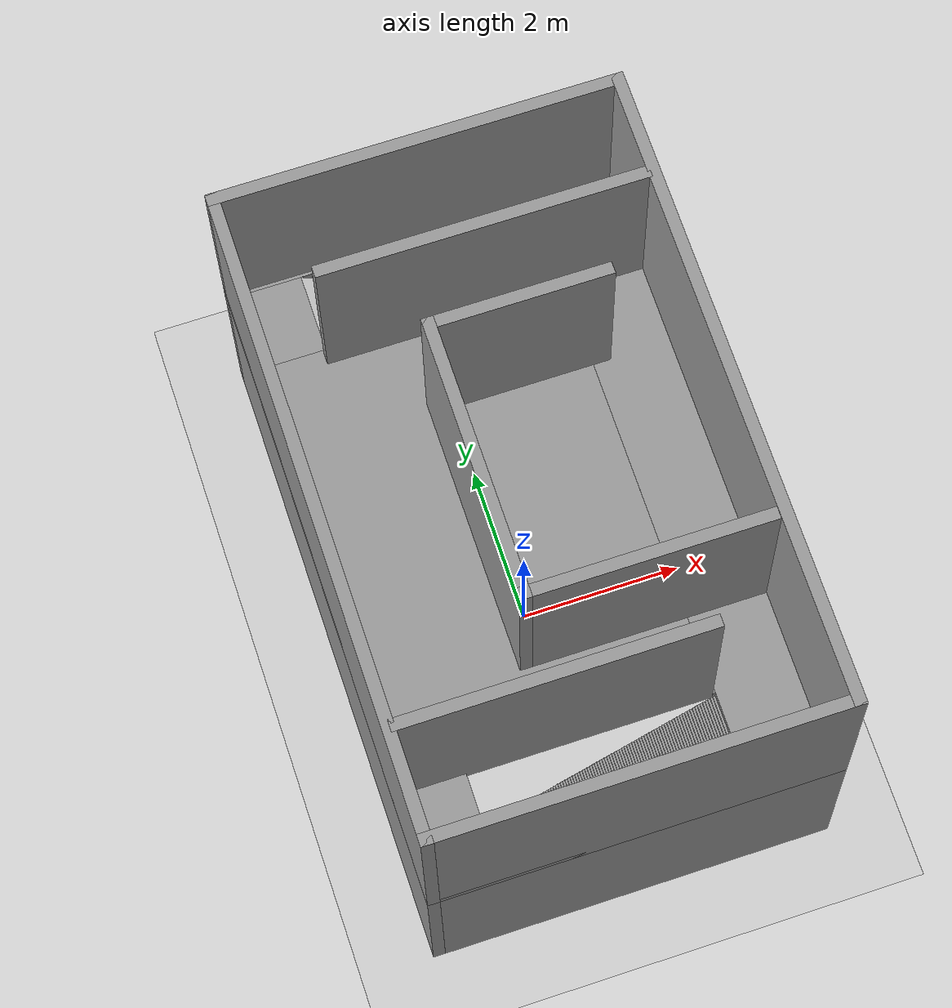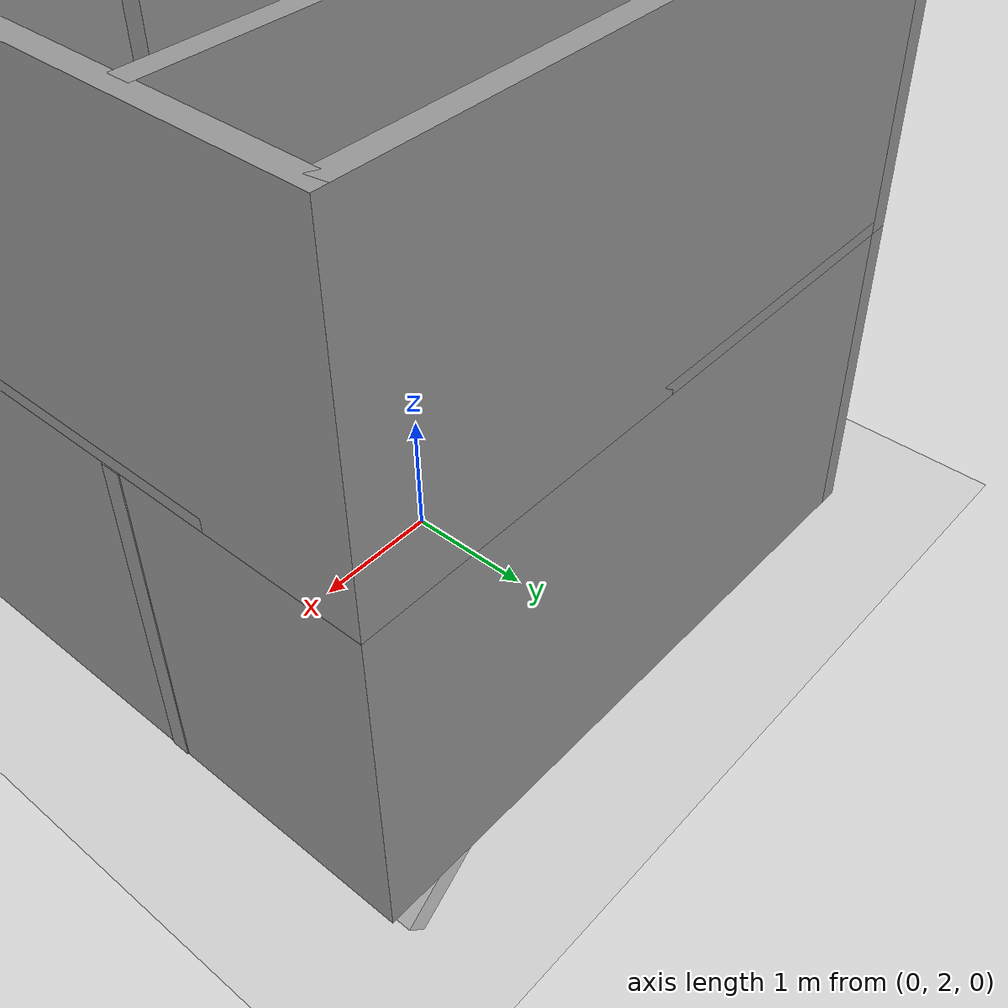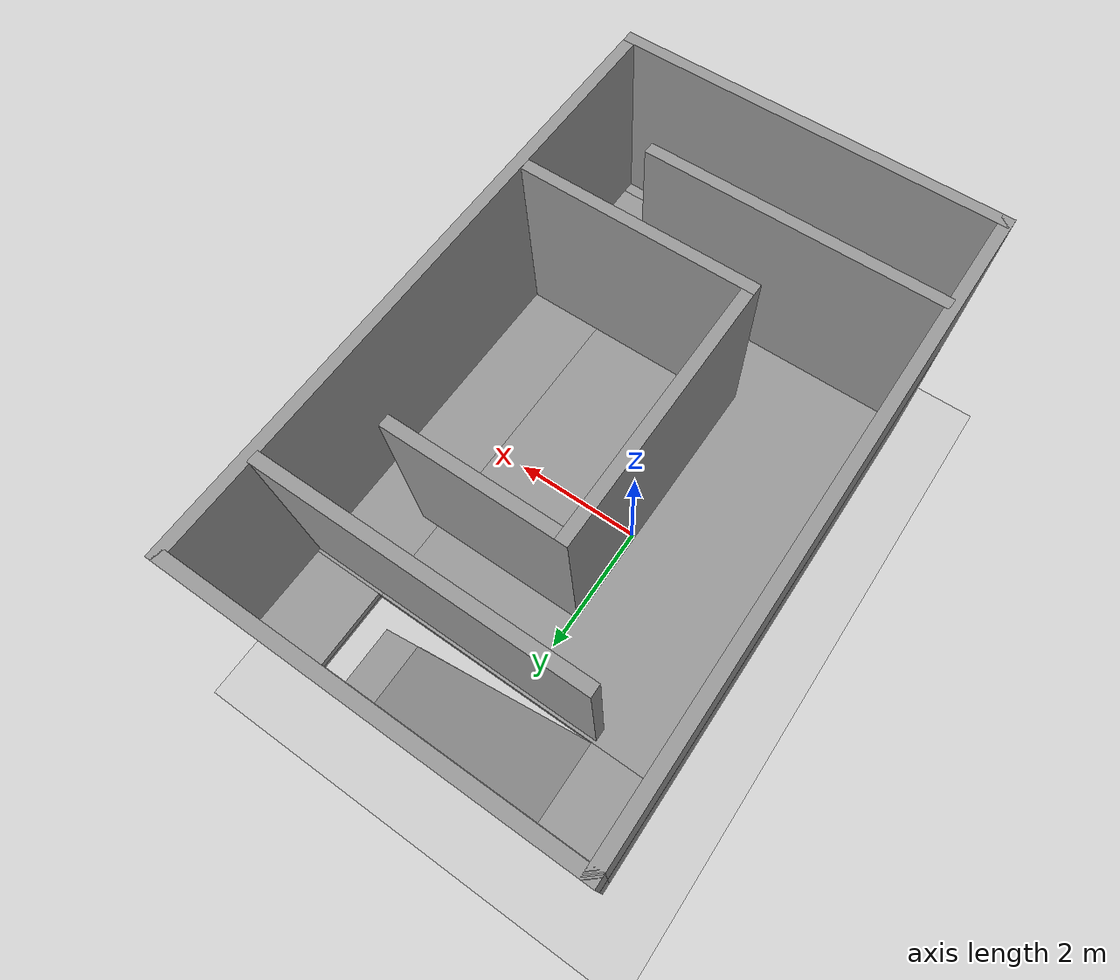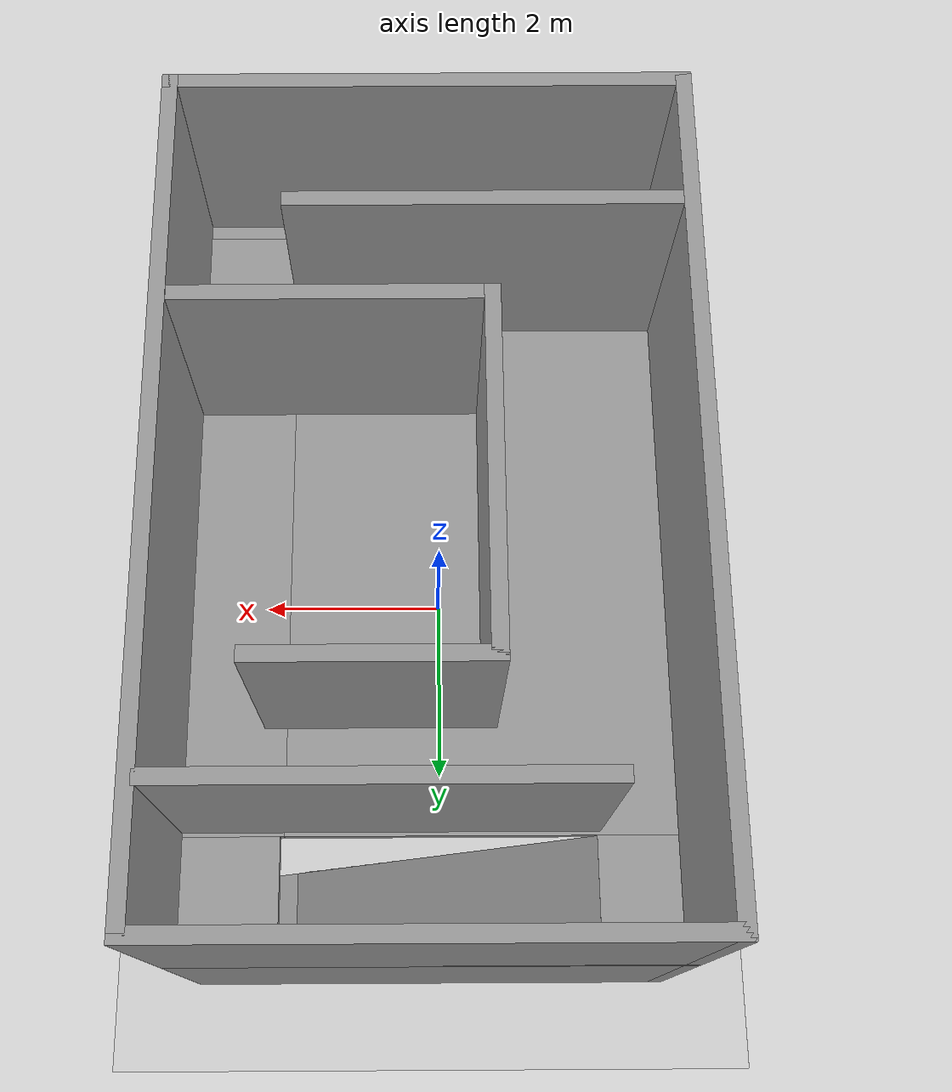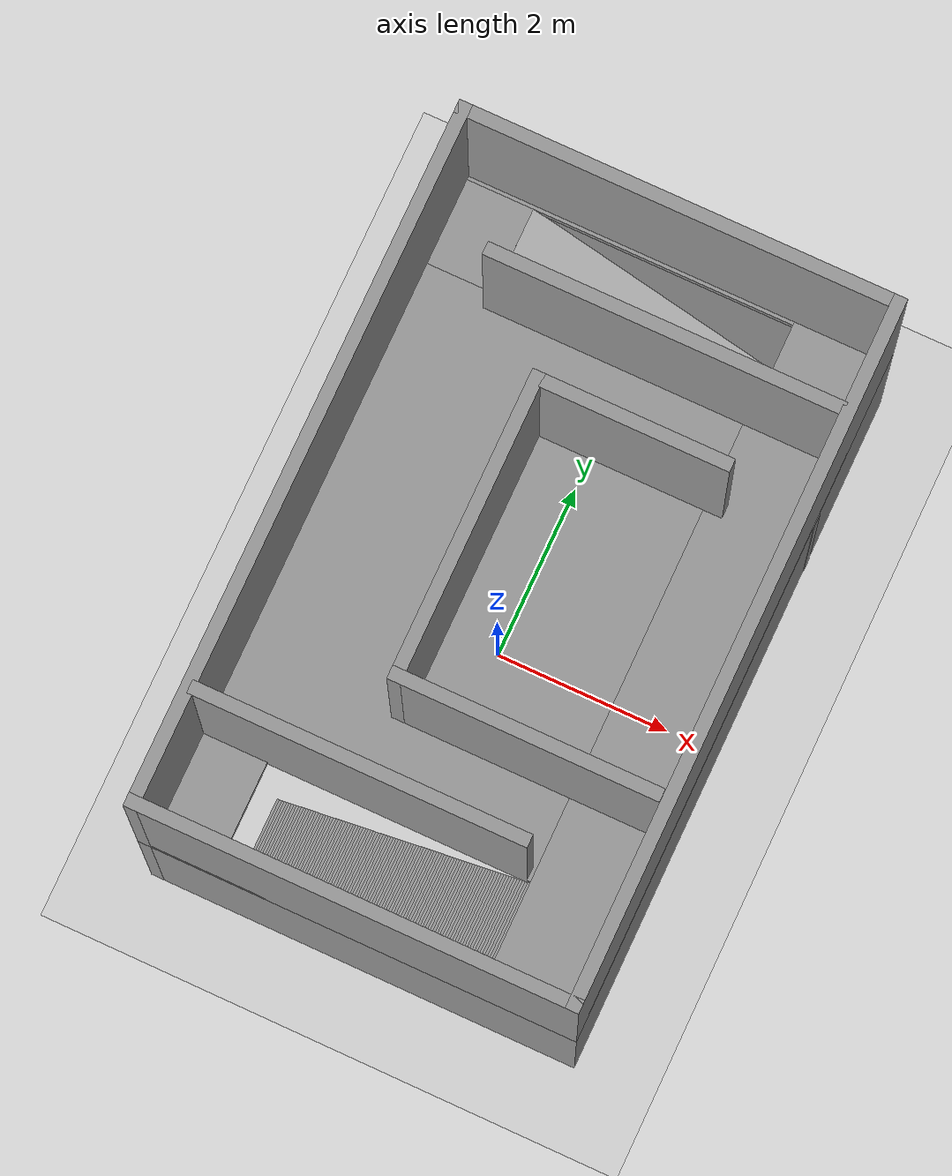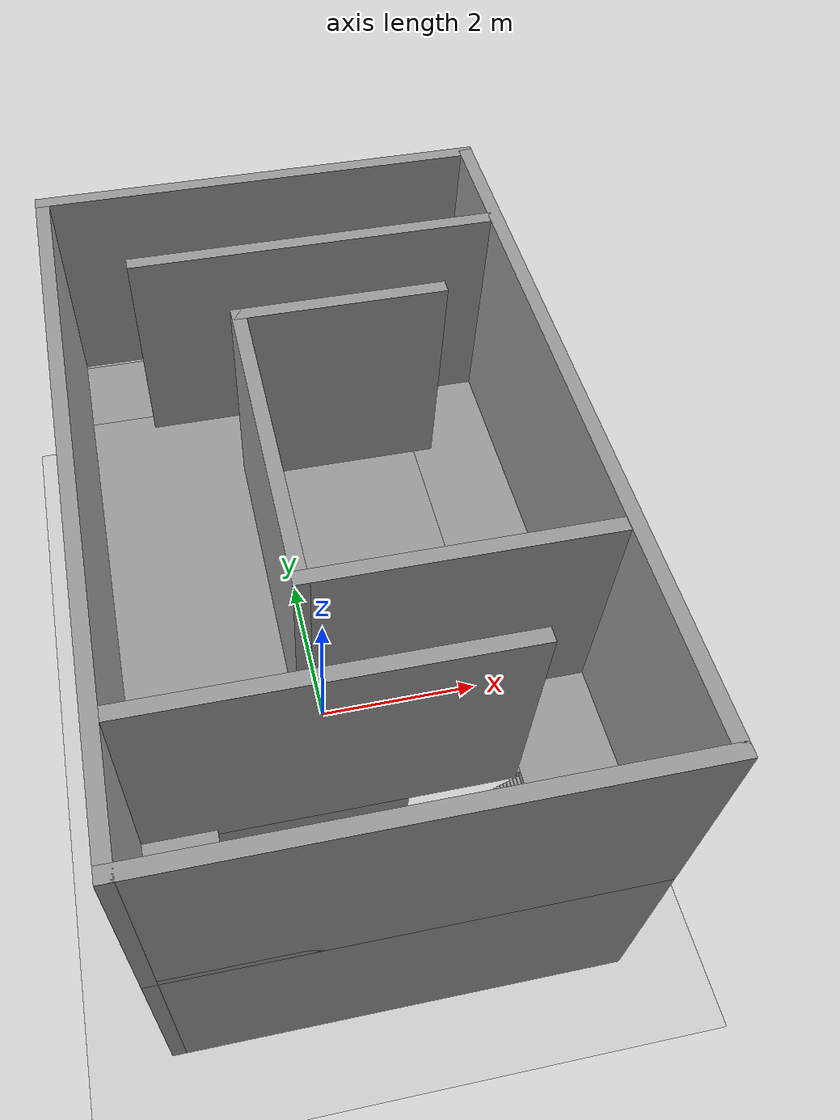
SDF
<sdf version="1.7">
 <world name="default">
  <model name="ground_plane">
   <static>1</static>
   <link name="link">
    <collision name="collision">
     <geometry><plane><normal>0 0 1</normal><size>100 100</size></plane></geometry>
     <surface>
      <contact><collide_bitmask>65535</collide_bitmask></contact>
      <friction><ode><mu>100</mu><mu2>50</mu2></ode></friction>
     </surface>
    </collision>
    <visual name="visual">
     <cast_shadows>0</cast_shadows>
     <geometry><plane><normal>0 0 1</normal><size>100 100</size></plane></geometry>
     <material>
      <script><uri>file://media/materials/scripts/gazebo.material</uri><name>Gazebo/Grey</name></script>
     </material>
    </visual>
   </link>
  </model>
  <light name="sun" type="directional">
   <pose>0 0 10 0 -0 0</pose>
   <diffuse>0.8 0.8 0.8 1</diffuse>
   <specular>0.2 0.2 0.2 1</specular>
   <attenuation>
    <range>1000</range>
    <constant>0.9</constant>
    <linear>0.01</linear>
    <quadratic>0.001</quadratic>
   </attenuation>
   <direction>-0.5 0.1 -0.9</direction>
   <spot><inner_angle>0</inner_angle><outer_angle>0</outer_angle><falloff>0</falloff></spot>
  </light>
  <model name="box">
   <static>1</static>
   <pose>0.369809 3.58329 0.898381 0 0.707317 0</pose>
   <link name="link">
    <collision name="collision"><geometry><box><size>5 1 0.2</size></box></geometry></collision>
    <visual name="visual"><geometry><box><size>5 1 0.2</size></box></geometry></visual>
   </link>
  </model>
  <gravity>0 0 -9.8</gravity>
  <magnetic_field>6e-06 2.3e-05 -4.2e-05</magnetic_field>
  <atmosphere type="adiabatic"/>
  <physics type="ode">
   <max_step_size>0.001</max_step_size>
   <real_time_factor>1</real_time_factor>
   <real_time_update_rate>1000</real_time_update_rate>
  </physics>
  <scene><ambient>0.4 0.4 0.4 1</ambient><background>0.7 0.7 0.7 1</background><shadows>1</shadows></scene>
  <spherical_coordinates>
   <surface_model>EARTH_WGS84</surface_model>
   <latitude_deg>0</latitude_deg>
   <longitude_deg>0</longitude_deg>
   <elevation>0</elevation>
   <heading_deg>0</heading_deg>
  </spherical_coordinates>
  <model name="test2">
   <pose>-0.713184 1.43074 0 0 -0 1.57047</pose>
   <link name="Floor_0">
    <pose>-1.16289 -0.828418 2.5 0 -0 0</pose>
    <visual name="Floor_0_Visual_0">
     <pose>-3.84843 0 0.05 0 -0 0</pose>
     <geometry><box><size>0.303133 5 0.1</size></box></geometry>
     <material>
      <script><uri>file://media/materials/scripts/gazebo.material</uri><name>Gazebo/Grey</name></script>
      <ambient>1 1 1 1</ambient>
     </material>
     <meta><layer>1</layer></meta>
    </visual>
    <collision name="Floor_0_Collision_0">
     <geometry><box><size>0.303133 5 0.1</size></box></geometry>
     <pose>-3.84843 0 0.05 0 -0 0</pose>
    </collision>
    <visual name="Floor_0_Visual_1">
     <pose>-0.443444 -1.94023 0.05 0 -0 0</pose>
     <geometry><box><size>6.50685 1.11955 0.1</size></box></geometry>
     <material>
      <script><uri>file://media/materials/scripts/gazebo.material</uri><name>Gazebo/Grey</name></script>
      <ambient>1 1 1 1</ambient>
     </material>
     <meta><layer>1</layer></meta>
    </visual>
    <collision name="Floor_0_Collision_1">
     <geometry><box><size>6.50685 1.11955 0.1</size></box></geometry>
     <pose>-0.443444 -1.94023 0.05 0 -0 0</pose>
    </collision>
    <visual name="Floor_0_Visual_2">
     <pose>3.40499 -1.96002 0.05 0 -0 0</pose>
     <geometry><box><size>1.19002 1.07996 0.1</size></box></geometry>
     <material>
      <script><uri>file://media/materials/scripts/gazebo.material</uri><name>Gazebo/Grey</name></script>
      <ambient>1 1 1 1</ambient>
     </material>
     <meta><layer>1</layer></meta>
    </visual>
    <collision name="Floor_0_Collision_2">
     <geometry><box><size>1.19002 1.07996 0.1</size></box></geometry>
     <pose>3.40499 -1.96002 0.05 0 -0 0</pose>
    </collision>
    <visual name="Floor_0_Visual_3">
     <pose>3.90499 0.539981 0.05 0 -0 0</pose>
     <geometry><box><size>0.19002 3.92004 0.1</size></box></geometry>
     <material>
      <script><uri>file://media/materials/scripts/gazebo.material</uri><name>Gazebo/Grey</name></script>
      <ambient>1 1 1 1</ambient>
     </material>
     <meta><layer>1</layer></meta>
    </visual>
    <collision name="Floor_0_Collision_3">
     <geometry><box><size>0.19002 3.92004 0.1</size></box></geometry>
     <pose>3.90499 0.539981 0.05 0 -0 0</pose>
    </collision>
    <visual name="Floor_0_Visual_4">
     <pose>0.056556 0.559775 0.05 0 -0 0</pose>
     <geometry><box><size>5.50685 3.88045 0.1</size></box></geometry>
     <material>
      <script><uri>file://media/materials/scripts/gazebo.material</uri><name>Gazebo/Grey</name></script>
      <ambient>1 1 1 1</ambient>
     </material>
     <meta><layer>1</layer></meta>
    </visual>
    <collision name="Floor_0_Collision_4">
     <geometry><box><size>5.50685 3.88045 0.1</size></box></geometry>
     <pose>0.056556 0.559775 0.05 0 -0 0</pose>
    </collision>
    <visual name="Floor_0_Visual_5">
     <pose>3.30998 2.03998 0.05 0 -0 0</pose>
     <geometry><box><size>1 0.920038 0.1</size></box></geometry>
     <material>
      <script><uri>file://media/materials/scripts/gazebo.material</uri><name>Gazebo/Grey</name></script>
      <ambient>1 1 1 1</ambient>
     </material>
     <meta><layer>1</layer></meta>
    </visual>
    <collision name="Floor_0_Collision_5">
     <geometry><box><size>1 0.920038 0.1</size></box></geometry>
     <pose>3.30998 2.03998 0.05 0 -0 0</pose>
    </collision>
    <visual name="Floor_0_Visual_6">
     <pose>-3.19687 2.05978 0.05 0 -0 0</pose>
     <geometry><box><size>1 0.88045 0.1</size></box></geometry>
     <material>
      <script><uri>file://media/materials/scripts/gazebo.material</uri><name>Gazebo/Grey</name></script>
      <ambient>1 1 1 1</ambient>
     </material>
     <meta><layer>1</layer></meta>
    </visual>
    <collision name="Floor_0_Collision_6">
     <geometry><box><size>1 0.88045 0.1</size></box></geometry>
     <pose>-3.19687 2.05978 0.05 0 -0 0</pose>
    </collision>
   </link>
   <link name="Stairs_4">
    <visual name="Stairs_4_Visual_0">
     <pose>-4.35976 0.776132 0.0125 0 -0 0</pose>
     <geometry><box><size>1 0.03 0.025</size></box></geometry>
     <material>
      <script><uri>file://media/materials/scripts/gazebo.material</uri><name>Gazebo/Grey</name></script>
      <ambient>1 1 1 1</ambient>
     </material>
     <meta><layer>0</layer></meta>
    </visual>
    <collision name="Stairs_4_Collision_0">
     <geometry><box><size>1 0.03 0.025</size></box></geometry>
     <pose>-4.35976 0.776132 0.0125 0 -0 0</pose>
    </collision>
    <visual name="Stairs_4_Visual_1">
     <pose>-4.35976 0.746132 0.0375 0 -0 0</pose>
     <geometry><box><size>1 0.03 0.025</size></box></geometry>
     <material>
      <script><uri>file://media/materials/scripts/gazebo.material</uri><name>Gazebo/Grey</name></script>
      <ambient>1 1 1 1</ambient>
     </material>
     <meta><layer>0</layer></meta>
    </visual>
    <collision name="Stairs_4_Collision_1">
     <geometry><box><size>1 0.03 0.025</size></box></geometry>
     <pose>-4.35976 0.746132 0.0375 0 -0 0</pose>
    </collision>
    <visual name="Stairs_4_Visual_2">
     <pose>-4.35976 0.716132 0.0625 0 -0 0</pose>
     <geometry><box><size>1 0.03 0.025</size></box></geometry>
     <material>
      <script><uri>file://media/materials/scripts/gazebo.material</uri><name>Gazebo/Grey</name></script>
      <ambient>1 1 1 1</ambient>
     </material>
     <meta><layer>0</layer></meta>
    </visual>
    <collision name="Stairs_4_Collision_2">
     <geometry><box><size>1 0.03 0.025</size></box></geometry>
     <pose>-4.35976 0.716132 0.0625 0 -0 0</pose>
    </collision>
    <visual name="Stairs_4_Visual_3">
     <pose>-4.35976 0.686132 0.0875 0 -0 0</pose>
     <geometry><box><size>1 0.03 0.025</size></box></geometry>
     <material>
      <script><uri>file://media/materials/scripts/gazebo.material</uri><name>Gazebo/Grey</name></script>
      <ambient>1 1 1 1</ambient>
     </material>
     <meta><layer>0</layer></meta>
    </visual>
    <collision name="Stairs_4_Collision_3">
     <geometry><box><size>1 0.03 0.025</size></box></geometry>
     <pose>-4.35976 0.686132 0.0875 0 -0 0</pose>
    </collision>
    <visual name="Stairs_4_Visual_4">
     <pose>-4.35976 0.656132 0.1125 0 -0 0</pose>
     <geometry><box><size>1 0.03 0.025</size></box></geometry>
     <material>
      <script><uri>file://media/materials/scripts/gazebo.material</uri><name>Gazebo/Grey</name></script>
      <ambient>1 1 1 1</ambient>
     </material>
     <meta><layer>0</layer></meta>
    </visual>
    <collision name="Stairs_4_Collision_4">
     <geometry><box><size>1 0.03 0.025</size></box></geometry>
     <pose>-4.35976 0.656132 0.1125 0 -0 0</pose>
    </collision>
    <visual name="Stairs_4_Visual_5">
     <pose>-4.35976 0.626132 0.1375 0 -0 0</pose>
     <geometry><box><size>1 0.03 0.025</size></box></geometry>
     <material>
      <script><uri>file://media/materials/scripts/gazebo.material</uri><name>Gazebo/Grey</name></script>
      <ambient>1 1 1 1</ambient>
     </material>
     <meta><layer>0</layer></meta>
    </visual>
    <collision name="Stairs_4_Collision_5">
     <geometry><box><size>1 0.03 0.025</size></box></geometry>
     <pose>-4.35976 0.626132 0.1375 0 -0 0</pose>
    </collision>
    <visual name="Stairs_4_Visual_6">
     <pose>-4.35976 0.596132 0.1625 0 -0 0</pose>
     <geometry><box><size>1 0.03 0.025</size></box></geometry>
     <material>
      <script><uri>file://media/materials/scripts/gazebo.material</uri><name>Gazebo/Grey</name></script>
      <ambient>1 1 1 1</ambient>
     </material>
     <meta><layer>0</layer></meta>
    </visual>
    <collision name="Stairs_4_Collision_6">
     <geometry><box><size>1 0.03 0.025</size></box></geometry>
     <pose>-4.35976 0.596132 0.1625 0 -0 0</pose>
    </collision>
    <visual name="Stairs_4_Visual_7">
     <pose>-4.35976 0.566132 0.1875 0 -0 0</pose>
     <geometry><box><size>1 0.03 0.025</size></box></geometry>
     <material>
      <script><uri>file://media/materials/scripts/gazebo.material</uri><name>Gazebo/Grey</name></script>
      <ambient>1 1 1 1</ambient>
     </material>
     <meta><layer>0</layer></meta>
    </visual>
    <collision name="Stairs_4_Collision_7">
     <geometry><box><size>1 0.03 0.025</size></box></geometry>
     <pose>-4.35976 0.566132 0.1875 0 -0 0</pose>
    </collision>
    <visual name="Stairs_4_Visual_8">
     <pose>-4.35976 0.536132 0.2125 0 -0 0</pose>
     <geometry><box><size>1 0.03 0.025</size></box></geometry>
     <material>
      <script><uri>file://media/materials/scripts/gazebo.material</uri><name>Gazebo/Grey</name></script>
      <ambient>1 1 1 1</ambient>
     </material>
     <meta><layer>0</layer></meta>
    </visual>
    <collision name="Stairs_4_Collision_8">
     <geometry><box><size>1 0.03 0.025</size></box></geometry>
     <pose>-4.35976 0.536132 0.2125 0 -0 0</pose>
    </collision>
    <visual name="Stairs_4_Visual_9">
     <pose>-4.35976 0.506132 0.2375 0 -0 0</pose>
     <geometry><box><size>1 0.03 0.025</size></box></geometry>
     <material>
      <script><uri>file://media/materials/scripts/gazebo.material</uri><name>Gazebo/Grey</name></script>
      <ambient>1 1 1 1</ambient>
     </material>
     <meta><layer>0</layer></meta>
    </visual>
    <collision name="Stairs_4_Collision_9">
     <geometry><box><size>1 0.03 0.025</size></box></geometry>
     <pose>-4.35976 0.506132 0.2375 0 -0 0</pose>
    </collision>
    <visual name="Stairs_4_Visual_10">
     <pose>-4.35976 0.476132 0.2625 0 -0 0</pose>
     <geometry><box><size>1 0.03 0.025</size></box></geometry>
     <material>
      <script><uri>file://media/materials/scripts/gazebo.material</uri><name>Gazebo/Grey</name></script>
      <ambient>1 1 1 1</ambient>
     </material>
     <meta><layer>0</layer></meta>
    </visual>
    <collision name="Stairs_4_Collision_10">
     <geometry><box><size>1 0.03 0.025</size></box></geometry>
     <pose>-4.35976 0.476132 0.2625 0 -0 0</pose>
    </collision>
    <visual name="Stairs_4_Visual_11">
     <pose>-4.35976 0.446132 0.2875 0 -0 0</pose>
     <geometry><box><size>1 0.03 0.025</size></box></geometry>
     <material>
      <script><uri>file://media/materials/scripts/gazebo.material</uri><name>Gazebo/Grey</name></script>
      <ambient>1 1 1 1</ambient>
     </material>
     <meta><layer>0</layer></meta>
    </visual>
    <collision name="Stairs_4_Collision_11">
     <geometry><box><size>1 0.03 0.025</size></box></geometry>
     <pose>-4.35976 0.446132 0.2875 0 -0 0</pose>
    </collision>
    <visual name="Stairs_4_Visual_12">
     <pose>-4.35976 0.416132 0.3125 0 -0 0</pose>
     <geometry><box><size>1 0.03 0.025</size></box></geometry>
     <material>
      <script><uri>file://media/materials/scripts/gazebo.material</uri><name>Gazebo/Grey</name></script>
      <ambient>1 1 1 1</ambient>
     </material>
     <meta><layer>0</layer></meta>
    </visual>
    <collision name="Stairs_4_Collision_12">
     <geometry><box><size>1 0.03 0.025</size></box></geometry>
     <pose>-4.35976 0.416132 0.3125 0 -0 0</pose>
    </collision>
    <visual name="Stairs_4_Visual_13">
     <pose>-4.35976 0.386132 0.3375 0 -0 0</pose>
     <geometry><box><size>1 0.03 0.025</size></box></geometry>
     <material>
      <script><uri>file://media/materials/scripts/gazebo.material</uri><name>Gazebo/Grey</name></script>
      <ambient>1 1 1 1</ambient>
     </material>
     <meta><layer>0</layer></meta>
    </visual>
    <collision name="Stairs_4_Collision_13">
     <geometry><box><size>1 0.03 0.025</size></box></geometry>
     <pose>-4.35976 0.386132 0.3375 0 -0 0</pose>
    </collision>
    <visual name="Stairs_4_Visual_14">
     <pose>-4.35976 0.356132 0.3625 0 -0 0</pose>
     <geometry><box><size>1 0.03 0.025</size></box></geometry>
     <material>
      <script><uri>file://media/materials/scripts/gazebo.material</uri><name>Gazebo/Grey</name></script>
      <ambient>1 1 1 1</ambient>
     </material>
     <meta><layer>0</layer></meta>
    </visual>
    <collision name="Stairs_4_Collision_14">
     <geometry><box><size>1 0.03 0.025</size></box></geometry>
     <pose>-4.35976 0.356132 0.3625 0 -0 0</pose>
    </collision>
    <visual name="Stairs_4_Visual_15">
     <pose>-4.35976 0.326132 0.3875 0 -0 0</pose>
     <geometry><box><size>1 0.03 0.025</size></box></geometry>
     <material>
      <script><uri>file://media/materials/scripts/gazebo.material</uri><name>Gazebo/Grey</name></script>
      <ambient>1 1 1 1</ambient>
     </material>
     <meta><layer>0</layer></meta>
    </visual>
    <collision name="Stairs_4_Collision_15">
     <geometry><box><size>1 0.03 0.025</size></box></geometry>
     <pose>-4.35976 0.326132 0.3875 0 -0 0</pose>
    </collision>
    <visual name="Stairs_4_Visual_16">
     <pose>-4.35976 0.296132 0.4125 0 -0 0</pose>
     <geometry><box><size>1 0.03 0.025</size></box></geometry>
     <material>
      <script><uri>file://media/materials/scripts/gazebo.material</uri><name>Gazebo/Grey</name></script>
      <ambient>1 1 1 1</ambient>
     </material>
     <meta><layer>0</layer></meta>
    </visual>
    <collision name="Stairs_4_Collision_16">
     <geometry><box><size>1 0.03 0.025</size></box></geometry>
     <pose>-4.35976 0.296132 0.4125 0 -0 0</pose>
    </collision>
    <visual name="Stairs_4_Visual_17">
     <pose>-4.35976 0.266132 0.4375 0 -0 0</pose>
     <geometry><box><size>1 0.03 0.025</size></box></geometry>
     <material>
      <script><uri>file://media/materials/scripts/gazebo.material</uri><name>Gazebo/Grey</name></script>
      <ambient>1 1 1 1</ambient>
     </material>
     <meta><layer>0</layer></meta>
    </visual>
    <collision name="Stairs_4_Collision_17">
     <geometry><box><size>1 0.03 0.025</size></box></geometry>
     <pose>-4.35976 0.266132 0.4375 0 -0 0</pose>
    </collision>
    <visual name="Stairs_4_Visual_18">
     <pose>-4.35976 0.236132 0.4625 0 -0 0</pose>
     <geometry><box><size>1 0.03 0.025</size></box></geometry>
     <material>
      <script><uri>file://media/materials/scripts/gazebo.material</uri><name>Gazebo/Grey</name></script>
      <ambient>1 1 1 1</ambient>
     </material>
     <meta><layer>0</layer></meta>
    </visual>
    <collision name="Stairs_4_Collision_18">
     <geometry><box><size>1 0.03 0.025</size></box></geometry>
     <pose>-4.35976 0.236132 0.4625 0 -0 0</pose>
    </collision>
    <visual name="Stairs_4_Visual_19">
     <pose>-4.35976 0.206132 0.4875 0 -0 0</pose>
     <geometry><box><size>1 0.03 0.025</size></box></geometry>
     <material>
      <script><uri>file://media/materials/scripts/gazebo.material</uri><name>Gazebo/Grey</name></script>
      <ambient>1 1 1 1</ambient>
     </material>
     <meta><layer>0</layer></meta>
    </visual>
    <collision name="Stairs_4_Collision_19">
     <geometry><box><size>1 0.03 0.025</size></box></geometry>
     <pose>-4.35976 0.206132 0.4875 0 -0 0</pose>
    </collision>
    <visual name="Stairs_4_Visual_20">
     <pose>-4.35976 0.176132 0.5125 0 -0 0</pose>
     <geometry><box><size>1 0.03 0.025</size></box></geometry>
     <material>
      <script><uri>file://media/materials/scripts/gazebo.material</uri><name>Gazebo/Grey</name></script>
      <ambient>1 1 1 1</ambient>
     </material>
     <meta><layer>0</layer></meta>
    </visual>
    <collision name="Stairs_4_Collision_20">
     <geometry><box><size>1 0.03 0.025</size></box></geometry>
     <pose>-4.35976 0.176132 0.5125 0 -0 0</pose>
    </collision>
    <visual name="Stairs_4_Visual_21">
     <pose>-4.35976 0.146132 0.5375 0 -0 0</pose>
     <geometry><box><size>1 0.03 0.025</size></box></geometry>
     <material>
      <script><uri>file://media/materials/scripts/gazebo.material</uri><name>Gazebo/Grey</name></script>
      <ambient>1 1 1 1</ambient>
     </material>
     <meta><layer>0</layer></meta>
    </visual>
    <collision name="Stairs_4_Collision_21">
     <geometry><box><size>1 0.03 0.025</size></box></geometry>
     <pose>-4.35976 0.146132 0.5375 0 -0 0</pose>
    </collision>
    <visual name="Stairs_4_Visual_22">
     <pose>-4.35976 0.116132 0.5625 0 -0 0</pose>
     <geometry><box><size>1 0.03 0.025</size></box></geometry>
     <material>
      <script><uri>file://media/materials/scripts/gazebo.material</uri><name>Gazebo/Grey</name></script>
      <ambient>1 1 1 1</ambient>
     </material>
     <meta><layer>0</layer></meta>
    </visual>
    <collision name="Stairs_4_Collision_22">
     <geometry><box><size>1 0.03 0.025</size></box></geometry>
     <pose>-4.35976 0.116132 0.5625 0 -0 0</pose>
    </collision>
    <visual name="Stairs_4_Visual_23">
     <pose>-4.35976 0.086132 0.5875 0 -0 0</pose>
     <geometry><box><size>1 0.03 0.025</size></box></geometry>
     <material>
      <script><uri>file://media/materials/scripts/gazebo.material</uri><name>Gazebo/Grey</name></script>
      <ambient>1 1 1 1</ambient>
     </material>
     <meta><layer>0</layer></meta>
    </visual>
    <collision name="Stairs_4_Collision_23">
     <geometry><box><size>1 0.03 0.025</size></box></geometry>
     <pose>-4.35976 0.086132 0.5875 0 -0 0</pose>
    </collision>
    <visual name="Stairs_4_Visual_24">
     <pose>-4.35976 0.056132 0.6125 0 -0 0</pose>
     <geometry><box><size>1 0.03 0.025</size></box></geometry>
     <material>
      <script><uri>file://media/materials/scripts/gazebo.material</uri><name>Gazebo/Grey</name></script>
      <ambient>1 1 1 1</ambient>
     </material>
     <meta><layer>0</layer></meta>
    </visual>
    <collision name="Stairs_4_Collision_24">
     <geometry><box><size>1 0.03 0.025</size></box></geometry>
     <pose>-4.35976 0.056132 0.6125 0 -0 0</pose>
    </collision>
    <visual name="Stairs_4_Visual_25">
     <pose>-4.35976 0.026132 0.6375 0 -0 0</pose>
     <geometry><box><size>1 0.03 0.025</size></box></geometry>
     <material>
      <script><uri>file://media/materials/scripts/gazebo.material</uri><name>Gazebo/Grey</name></script>
      <ambient>1 1 1 1</ambient>
     </material>
     <meta><layer>0</layer></meta>
    </visual>
    <collision name="Stairs_4_Collision_25">
     <geometry><box><size>1 0.03 0.025</size></box></geometry>
     <pose>-4.35976 0.026132 0.6375 0 -0 0</pose>
    </collision>
    <visual name="Stairs_4_Visual_26">
     <pose>-4.35976 -0.003868 0.6625 0 -0 0</pose>
     <geometry><box><size>1 0.03 0.025</size></box></geometry>
     <material>
      <script><uri>file://media/materials/scripts/gazebo.material</uri><name>Gazebo/Grey</name></script>
      <ambient>1 1 1 1</ambient>
     </material>
     <meta><layer>0</layer></meta>
    </visual>
    <collision name="Stairs_4_Collision_26">
     <geometry><box><size>1 0.03 0.025</size></box></geometry>
     <pose>-4.35976 -0.003868 0.6625 0 -0 0</pose>
    </collision>
    <visual name="Stairs_4_Visual_27">
     <pose>-4.35976 -0.033868 0.6875 0 -0 0</pose>
     <geometry><box><size>1 0.03 0.025</size></box></geometry>
     <material>
      <script><uri>file://media/materials/scripts/gazebo.material</uri><name>Gazebo/Grey</name></script>
      <ambient>1 1 1 1</ambient>
     </material>
     <meta><layer>0</layer></meta>
    </visual>
    <collision name="Stairs_4_Collision_27">
     <geometry><box><size>1 0.03 0.025</size></box></geometry>
     <pose>-4.35976 -0.033868 0.6875 0 -0 0</pose>
    </collision>
    <visual name="Stairs_4_Visual_28">
     <pose>-4.35976 -0.063868 0.7125 0 -0 0</pose>
     <geometry><box><size>1 0.03 0.025</size></box></geometry>
     <material>
      <script><uri>file://media/materials/scripts/gazebo.material</uri><name>Gazebo/Grey</name></script>
      <ambient>1 1 1 1</ambient>
     </material>
     <meta><layer>0</layer></meta>
    </visual>
    <collision name="Stairs_4_Collision_28">
     <geometry><box><size>1 0.03 0.025</size></box></geometry>
     <pose>-4.35976 -0.063868 0.7125 0 -0 0</pose>
    </collision>
    <visual name="Stairs_4_Visual_29">
     <pose>-4.35976 -0.093868 0.7375 0 -0 0</pose>
     <geometry><box><size>1 0.03 0.025</size></box></geometry>
     <material>
      <script><uri>file://media/materials/scripts/gazebo.material</uri><name>Gazebo/Grey</name></script>
      <ambient>1 1 1 1</ambient>
     </material>
     <meta><layer>0</layer></meta>
    </visual>
    <collision name="Stairs_4_Collision_29">
     <geometry><box><size>1 0.03 0.025</size></box></geometry>
     <pose>-4.35976 -0.093868 0.7375 0 -0 0</pose>
    </collision>
    <visual name="Stairs_4_Visual_30">
     <pose>-4.35976 -0.123868 0.7625 0 -0 0</pose>
     <geometry><box><size>1 0.03 0.025</size></box></geometry>
     <material>
      <script><uri>file://media/materials/scripts/gazebo.material</uri><name>Gazebo/Grey</name></script>
      <ambient>1 1 1 1</ambient>
     </material>
     <meta><layer>0</layer></meta>
    </visual>
    <collision name="Stairs_4_Collision_30">
     <geometry><box><size>1 0.03 0.025</size></box></geometry>
     <pose>-4.35976 -0.123868 0.7625 0 -0 0</pose>
    </collision>
    <visual name="Stairs_4_Visual_31">
     <pose>-4.35976 -0.153868 0.7875 0 -0 0</pose>
     <geometry><box><size>1 0.03 0.025</size></box></geometry>
     <material>
      <script><uri>file://media/materials/scripts/gazebo.material</uri><name>Gazebo/Grey</name></script>
      <ambient>1 1 1 1</ambient>
     </material>
     <meta><layer>0</layer></meta>
    </visual>
    <collision name="Stairs_4_Collision_31">
     <geometry><box><size>1 0.03 0.025</size></box></geometry>
     <pose>-4.35976 -0.153868 0.7875 0 -0 0</pose>
    </collision>
    <visual name="Stairs_4_Visual_32">
     <pose>-4.35976 -0.183868 0.8125 0 -0 0</pose>
     <geometry><box><size>1 0.03 0.025</size></box></geometry>
     <material>
      <script><uri>file://media/materials/scripts/gazebo.material</uri><name>Gazebo/Grey</name></script>
      <ambient>1 1 1 1</ambient>
     </material>
     <meta><layer>0</layer></meta>
    </visual>
    <collision name="Stairs_4_Collision_32">
     <geometry><box><size>1 0.03 0.025</size></box></geometry>
     <pose>-4.35976 -0.183868 0.8125 0 -0 0</pose>
    </collision>
    <visual name="Stairs_4_Visual_33">
     <pose>-4.35976 -0.213868 0.8375 0 -0 0</pose>
     <geometry><box><size>1 0.03 0.025</size></box></geometry>
     <material>
      <script><uri>file://media/materials/scripts/gazebo.material</uri><name>Gazebo/Grey</name></script>
      <ambient>1 1 1 1</ambient>
     </material>
     <meta><layer>0</layer></meta>
    </visual>
    <collision name="Stairs_4_Collision_33">
     <geometry><box><size>1 0.03 0.025</size></box></geometry>
     <pose>-4.35976 -0.213868 0.8375 0 -0 0</pose>
    </collision>
    <visual name="Stairs_4_Visual_34">
     <pose>-4.35976 -0.243868 0.8625 0 -0 0</pose>
     <geometry><box><size>1 0.03 0.025</size></box></geometry>
     <material>
      <script><uri>file://media/materials/scripts/gazebo.material</uri><name>Gazebo/Grey</name></script>
      <ambient>1 1 1 1</ambient>
     </material>
     <meta><layer>0</layer></meta>
    </visual>
    <collision name="Stairs_4_Collision_34">
     <geometry><box><size>1 0.03 0.025</size></box></geometry>
     <pose>-4.35976 -0.243868 0.8625 0 -0 0</pose>
    </collision>
    <visual name="Stairs_4_Visual_35">
     <pose>-4.35976 -0.273868 0.8875 0 -0 0</pose>
     <geometry><box><size>1 0.03 0.025</size></box></geometry>
     <material>
      <script><uri>file://media/materials/scripts/gazebo.material</uri><name>Gazebo/Grey</name></script>
      <ambient>1 1 1 1</ambient>
     </material>
     <meta><layer>0</layer></meta>
    </visual>
    <collision name="Stairs_4_Collision_35">
     <geometry><box><size>1 0.03 0.025</size></box></geometry>
     <pose>-4.35976 -0.273868 0.8875 0 -0 0</pose>
    </collision>
    <visual name="Stairs_4_Visual_36">
     <pose>-4.35976 -0.303868 0.9125 0 -0 0</pose>
     <geometry><box><size>1 0.03 0.025</size></box></geometry>
     <material>
      <script><uri>file://media/materials/scripts/gazebo.material</uri><name>Gazebo/Grey</name></script>
      <ambient>1 1 1 1</ambient>
     </material>
     <meta><layer>0</layer></meta>
    </visual>
    <collision name="Stairs_4_Collision_36">
     <geometry><box><size>1 0.03 0.025</size></box></geometry>
     <pose>-4.35976 -0.303868 0.9125 0 -0 0</pose>
    </collision>
    <visual name="Stairs_4_Visual_37">
     <pose>-4.35976 -0.333868 0.9375 0 -0 0</pose>
     <geometry><box><size>1 0.03 0.025</size></box></geometry>
     <material>
      <script><uri>file://media/materials/scripts/gazebo.material</uri><name>Gazebo/Grey</name></script>
      <ambient>1 1 1 1</ambient>
     </material>
     <meta><layer>0</layer></meta>
    </visual>
    <collision name="Stairs_4_Collision_37">
     <geometry><box><size>1 0.03 0.025</size></box></geometry>
     <pose>-4.35976 -0.333868 0.9375 0 -0 0</pose>
    </collision>
    <visual name="Stairs_4_Visual_38">
     <pose>-4.35976 -0.363868 0.9625 0 -0 0</pose>
     <geometry><box><size>1 0.03 0.025</size></box></geometry>
     <material>
      <script><uri>file://media/materials/scripts/gazebo.material</uri><name>Gazebo/Grey</name></script>
      <ambient>1 1 1 1</ambient>
     </material>
     <meta><layer>0</layer></meta>
    </visual>
    <collision name="Stairs_4_Collision_38">
     <geometry><box><size>1 0.03 0.025</size></box></geometry>
     <pose>-4.35976 -0.363868 0.9625 0 -0 0</pose>
    </collision>
    <visual name="Stairs_4_Visual_39">
     <pose>-4.35976 -0.393868 0.9875 0 -0 0</pose>
     <geometry><box><size>1 0.03 0.025</size></box></geometry>
     <material>
      <script><uri>file://media/materials/scripts/gazebo.material</uri><name>Gazebo/Grey</name></script>
      <ambient>1 1 1 1</ambient>
     </material>
     <meta><layer>0</layer></meta>
    </visual>
    <collision name="Stairs_4_Collision_39">
     <geometry><box><size>1 0.03 0.025</size></box></geometry>
     <pose>-4.35976 -0.393868 0.9875 0 -0 0</pose>
    </collision>
    <visual name="Stairs_4_Visual_40">
     <pose>-4.35976 -0.423868 1.0125 0 -0 0</pose>
     <geometry><box><size>1 0.03 0.025</size></box></geometry>
     <material>
      <script><uri>file://media/materials/scripts/gazebo.material</uri><name>Gazebo/Grey</name></script>
      <ambient>1 1 1 1</ambient>
     </material>
     <meta><layer>0</layer></meta>
    </visual>
    <collision name="Stairs_4_Collision_40">
     <geometry><box><size>1 0.03 0.025</size></box></geometry>
     <pose>-4.35976 -0.423868 1.0125 0 -0 0</pose>
    </collision>
    <visual name="Stairs_4_Visual_41">
     <pose>-4.35976 -0.453868 1.0375 0 -0 0</pose>
     <geometry><box><size>1 0.03 0.025</size></box></geometry>
     <material>
      <script><uri>file://media/materials/scripts/gazebo.material</uri><name>Gazebo/Grey</name></script>
      <ambient>1 1 1 1</ambient>
     </material>
     <meta><layer>0</layer></meta>
    </visual>
    <collision name="Stairs_4_Collision_41">
     <geometry><box><size>1 0.03 0.025</size></box></geometry>
     <pose>-4.35976 -0.453868 1.0375 0 -0 0</pose>
    </collision>
    <visual name="Stairs_4_Visual_42">
     <pose>-4.35976 -0.483868 1.0625 0 -0 0</pose>
     <geometry><box><size>1 0.03 0.025</size></box></geometry>
     <material>
      <script><uri>file://media/materials/scripts/gazebo.material</uri><name>Gazebo/Grey</name></script>
      <ambient>1 1 1 1</ambient>
     </material>
     <meta><layer>0</layer></meta>
    </visual>
    <collision name="Stairs_4_Collision_42">
     <geometry><box><size>1 0.03 0.025</size></box></geometry>
     <pose>-4.35976 -0.483868 1.0625 0 -0 0</pose>
    </collision>
    <visual name="Stairs_4_Visual_43">
     <pose>-4.35976 -0.513868 1.0875 0 -0 0</pose>
     <geometry><box><size>1 0.03 0.025</size></box></geometry>
     <material>
      <script><uri>file://media/materials/scripts/gazebo.material</uri><name>Gazebo/Grey</name></script>
      <ambient>1 1 1 1</ambient>
     </material>
     <meta><layer>0</layer></meta>
    </visual>
    <collision name="Stairs_4_Collision_43">
     <geometry><box><size>1 0.03 0.025</size></box></geometry>
     <pose>-4.35976 -0.513868 1.0875 0 -0 0</pose>
    </collision>
    <visual name="Stairs_4_Visual_44">
     <pose>-4.35976 -0.543868 1.1125 0 -0 0</pose>
     <geometry><box><size>1 0.03 0.025</size></box></geometry>
     <material>
      <script><uri>file://media/materials/scripts/gazebo.material</uri><name>Gazebo/Grey</name></script>
      <ambient>1 1 1 1</ambient>
     </material>
     <meta><layer>0</layer></meta>
    </visual>
    <collision name="Stairs_4_Collision_44">
     <geometry><box><size>1 0.03 0.025</size></box></geometry>
     <pose>-4.35976 -0.543868 1.1125 0 -0 0</pose>
    </collision>
    <visual name="Stairs_4_Visual_45">
     <pose>-4.35976 -0.573868 1.1375 0 -0 0</pose>
     <geometry><box><size>1 0.03 0.025</size></box></geometry>
     <material>
      <script><uri>file://media/materials/scripts/gazebo.material</uri><name>Gazebo/Grey</name></script>
      <ambient>1 1 1 1</ambient>
     </material>
     <meta><layer>0</layer></meta>
    </visual>
    <collision name="Stairs_4_Collision_45">
     <geometry><box><size>1 0.03 0.025</size></box></geometry>
     <pose>-4.35976 -0.573868 1.1375 0 -0 0</pose>
    </collision>
    <visual name="Stairs_4_Visual_46">
     <pose>-4.35976 -0.603868 1.1625 0 -0 0</pose>
     <geometry><box><size>1 0.03 0.025</size></box></geometry>
     <material>
      <script><uri>file://media/materials/scripts/gazebo.material</uri><name>Gazebo/Grey</name></script>
      <ambient>1 1 1 1</ambient>
     </material>
     <meta><layer>0</layer></meta>
    </visual>
    <collision name="Stairs_4_Collision_46">
     <geometry><box><size>1 0.03 0.025</size></box></geometry>
     <pose>-4.35976 -0.603868 1.1625 0 -0 0</pose>
    </collision>
    <visual name="Stairs_4_Visual_47">
     <pose>-4.35976 -0.633868 1.1875 0 -0 0</pose>
     <geometry><box><size>1 0.03 0.025</size></box></geometry>
     <material>
      <script><uri>file://media/materials/scripts/gazebo.material</uri><name>Gazebo/Grey</name></script>
      <ambient>1 1 1 1</ambient>
     </material>
     <meta><layer>0</layer></meta>
    </visual>
    <collision name="Stairs_4_Collision_47">
     <geometry><box><size>1 0.03 0.025</size></box></geometry>
     <pose>-4.35976 -0.633868 1.1875 0 -0 0</pose>
    </collision>
    <visual name="Stairs_4_Visual_48">
     <pose>-4.35976 -0.663868 1.2125 0 -0 0</pose>
     <geometry><box><size>1 0.03 0.025</size></box></geometry>
     <material>
      <script><uri>file://media/materials/scripts/gazebo.material</uri><name>Gazebo/Grey</name></script>
      <ambient>1 1 1 1</ambient>
     </material>
     <meta><layer>0</layer></meta>
    </visual>
    <collision name="Stairs_4_Collision_48">
     <geometry><box><size>1 0.03 0.025</size></box></geometry>
     <pose>-4.35976 -0.663868 1.2125 0 -0 0</pose>
    </collision>
    <visual name="Stairs_4_Visual_49">
     <pose>-4.35976 -0.693868 1.2375 0 -0 0</pose>
     <geometry><box><size>1 0.03 0.025</size></box></geometry>
     <material>
      <script><uri>file://media/materials/scripts/gazebo.material</uri><name>Gazebo/Grey</name></script>
      <ambient>1 1 1 1</ambient>
     </material>
     <meta><layer>0</layer></meta>
    </visual>
    <collision name="Stairs_4_Collision_49">
     <geometry><box><size>1 0.03 0.025</size></box></geometry>
     <pose>-4.35976 -0.693868 1.2375 0 -0 0</pose>
    </collision>
    <visual name="Stairs_4_Visual_50">
     <pose>-4.35976 -0.723868 1.2625 0 -0 0</pose>
     <geometry><box><size>1 0.03 0.025</size></box></geometry>
     <material>
      <script><uri>file://media/materials/scripts/gazebo.material</uri><name>Gazebo/Grey</name></script>
      <ambient>1 1 1 1</ambient>
     </material>
     <meta><layer>0</layer></meta>
    </visual>
    <collision name="Stairs_4_Collision_50">
     <geometry><box><size>1 0.03 0.025</size></box></geometry>
     <pose>-4.35976 -0.723868 1.2625 0 -0 0</pose>
    </collision>
    <visual name="Stairs_4_Visual_51">
     <pose>-4.35976 -0.753868 1.2875 0 -0 0</pose>
     <geometry><box><size>1 0.03 0.025</size></box></geometry>
     <material>
      <script><uri>file://media/materials/scripts/gazebo.material</uri><name>Gazebo/Grey</name></script>
      <ambient>1 1 1 1</ambient>
     </material>
     <meta><layer>0</layer></meta>
    </visual>
    <collision name="Stairs_4_Collision_51">
     <geometry><box><size>1 0.03 0.025</size></box></geometry>
     <pose>-4.35976 -0.753868 1.2875 0 -0 0</pose>
    </collision>
    <visual name="Stairs_4_Visual_52">
     <pose>-4.35976 -0.783868 1.3125 0 -0 0</pose>
     <geometry><box><size>1 0.03 0.025</size></box></geometry>
     <material>
      <script><uri>file://media/materials/scripts/gazebo.material</uri><name>Gazebo/Grey</name></script>
      <ambient>1 1 1 1</ambient>
     </material>
     <meta><layer>0</layer></meta>
    </visual>
    <collision name="Stairs_4_Collision_52">
     <geometry><box><size>1 0.03 0.025</size></box></geometry>
     <pose>-4.35976 -0.783868 1.3125 0 -0 0</pose>
    </collision>
    <visual name="Stairs_4_Visual_53">
     <pose>-4.35976 -0.813868 1.3375 0 -0 0</pose>
     <geometry><box><size>1 0.03 0.025</size></box></geometry>
     <material>
      <script><uri>file://media/materials/scripts/gazebo.material</uri><name>Gazebo/Grey</name></script>
      <ambient>1 1 1 1</ambient>
     </material>
     <meta><layer>0</layer></meta>
    </visual>
    <collision name="Stairs_4_Collision_53">
     <geometry><box><size>1 0.03 0.025</size></box></geometry>
     <pose>-4.35976 -0.813868 1.3375 0 -0 0</pose>
    </collision>
    <visual name="Stairs_4_Visual_54">
     <pose>-4.35976 -0.843868 1.3625 0 -0 0</pose>
     <geometry><box><size>1 0.03 0.025</size></box></geometry>
     <material>
      <script><uri>file://media/materials/scripts/gazebo.material</uri><name>Gazebo/Grey</name></script>
      <ambient>1 1 1 1</ambient>
     </material>
     <meta><layer>0</layer></meta>
    </visual>
    <collision name="Stairs_4_Collision_54">
     <geometry><box><size>1 0.03 0.025</size></box></geometry>
     <pose>-4.35976 -0.843868 1.3625 0 -0 0</pose>
    </collision>
    <visual name="Stairs_4_Visual_55">
     <pose>-4.35976 -0.873868 1.3875 0 -0 0</pose>
     <geometry><box><size>1 0.03 0.025</size></box></geometry>
     <material>
      <script><uri>file://media/materials/scripts/gazebo.material</uri><name>Gazebo/Grey</name></script>
      <ambient>1 1 1 1</ambient>
     </material>
     <meta><layer>0</layer></meta>
    </visual>
    <collision name="Stairs_4_Collision_55">
     <geometry><box><size>1 0.03 0.025</size></box></geometry>
     <pose>-4.35976 -0.873868 1.3875 0 -0 0</pose>
    </collision>
    <visual name="Stairs_4_Visual_56">
     <pose>-4.35976 -0.903868 1.4125 0 -0 0</pose>
     <geometry><box><size>1 0.03 0.025</size></box></geometry>
     <material>
      <script><uri>file://media/materials/scripts/gazebo.material</uri><name>Gazebo/Grey</name></script>
      <ambient>1 1 1 1</ambient>
     </material>
     <meta><layer>0</layer></meta>
    </visual>
    <collision name="Stairs_4_Collision_56">
     <geometry><box><size>1 0.03 0.025</size></box></geometry>
     <pose>-4.35976 -0.903868 1.4125 0 -0 0</pose>
    </collision>
    <visual name="Stairs_4_Visual_57">
     <pose>-4.35976 -0.933868 1.4375 0 -0 0</pose>
     <geometry><box><size>1 0.03 0.025</size></box></geometry>
     <material>
      <script><uri>file://media/materials/scripts/gazebo.material</uri><name>Gazebo/Grey</name></script>
      <ambient>1 1 1 1</ambient>
     </material>
     <meta><layer>0</layer></meta>
    </visual>
    <collision name="Stairs_4_Collision_57">
     <geometry><box><size>1 0.03 0.025</size></box></geometry>
     <pose>-4.35976 -0.933868 1.4375 0 -0 0</pose>
    </collision>
    <visual name="Stairs_4_Visual_58">
     <pose>-4.35976 -0.963868 1.4625 0 -0 0</pose>
     <geometry><box><size>1 0.03 0.025</size></box></geometry>
     <material>
      <script><uri>file://media/materials/scripts/gazebo.material</uri><name>Gazebo/Grey</name></script>
      <ambient>1 1 1 1</ambient>
     </material>
     <meta><layer>0</layer></meta>
    </visual>
    <collision name="Stairs_4_Collision_58">
     <geometry><box><size>1 0.03 0.025</size></box></geometry>
     <pose>-4.35976 -0.963868 1.4625 0 -0 0</pose>
    </collision>
    <visual name="Stairs_4_Visual_59">
     <pose>-4.35976 -0.993868 1.4875 0 -0 0</pose>
     <geometry><box><size>1 0.03 0.025</size></box></geometry>
     <material>
      <script><uri>file://media/materials/scripts/gazebo.material</uri><name>Gazebo/Grey</name></script>
      <ambient>1 1 1 1</ambient>
     </material>
     <meta><layer>0</layer></meta>
    </visual>
    <collision name="Stairs_4_Collision_59">
     <geometry><box><size>1 0.03 0.025</size></box></geometry>
     <pose>-4.35976 -0.993868 1.4875 0 -0 0</pose>
    </collision>
    <visual name="Stairs_4_Visual_60">
     <pose>-4.35976 -1.02387 1.5125 0 -0 0</pose>
     <geometry><box><size>1 0.03 0.025</size></box></geometry>
     <material>
      <script><uri>file://media/materials/scripts/gazebo.material</uri><name>Gazebo/Grey</name></script>
      <ambient>1 1 1 1</ambient>
     </material>
     <meta><layer>0</layer></meta>
    </visual>
    <collision name="Stairs_4_Collision_60">
     <geometry><box><size>1 0.03 0.025</size></box></geometry>
     <pose>-4.35976 -1.02387 1.5125 0 -0 0</pose>
    </collision>
    <visual name="Stairs_4_Visual_61">
     <pose>-4.35976 -1.05387 1.5375 0 -0 0</pose>
     <geometry><box><size>1 0.03 0.025</size></box></geometry>
     <material>
      <script><uri>file://media/materials/scripts/gazebo.material</uri><name>Gazebo/Grey</name></script>
      <ambient>1 1 1 1</ambient>
     </material>
     <meta><layer>0</layer></meta>
    </visual>
    <collision name="Stairs_4_Collision_61">
     <geometry><box><size>1 0.03 0.025</size></box></geometry>
     <pose>-4.35976 -1.05387 1.5375 0 -0 0</pose>
    </collision>
    <visual name="Stairs_4_Visual_62">
     <pose>-4.35976 -1.08387 1.5625 0 -0 0</pose>
     <geometry><box><size>1 0.03 0.025</size></box></geometry>
     <material>
      <script><uri>file://media/materials/scripts/gazebo.material</uri><name>Gazebo/Grey</name></script>
      <ambient>1 1 1 1</ambient>
     </material>
     <meta><layer>0</layer></meta>
    </visual>
    <collision name="Stairs_4_Collision_62">
     <geometry><box><size>1 0.03 0.025</size></box></geometry>
     <pose>-4.35976 -1.08387 1.5625 0 -0 0</pose>
    </collision>
    <visual name="Stairs_4_Visual_63">
     <pose>-4.35976 -1.11387 1.5875 0 -0 0</pose>
     <geometry><box><size>1 0.03 0.025</size></box></geometry>
     <material>
      <script><uri>file://media/materials/scripts/gazebo.material</uri><name>Gazebo/Grey</name></script>
      <ambient>1 1 1 1</ambient>
     </material>
     <meta><layer>0</layer></meta>
    </visual>
    <collision name="Stairs_4_Collision_63">
     <geometry><box><size>1 0.03 0.025</size></box></geometry>
     <pose>-4.35976 -1.11387 1.5875 0 -0 0</pose>
    </collision>
    <visual name="Stairs_4_Visual_64">
     <pose>-4.35976 -1.14387 1.6125 0 -0 0</pose>
     <geometry><box><size>1 0.03 0.025</size></box></geometry>
     <material>
      <script><uri>file://media/materials/scripts/gazebo.material</uri><name>Gazebo/Grey</name></script>
      <ambient>1 1 1 1</ambient>
     </material>
     <meta><layer>0</layer></meta>
    </visual>
    <collision name="Stairs_4_Collision_64">
     <geometry><box><size>1 0.03 0.025</size></box></geometry>
     <pose>-4.35976 -1.14387 1.6125 0 -0 0</pose>
    </collision>
    <visual name="Stairs_4_Visual_65">
     <pose>-4.35976 -1.17387 1.6375 0 -0 0</pose>
     <geometry><box><size>1 0.03 0.025</size></box></geometry>
     <material>
      <script><uri>file://media/materials/scripts/gazebo.material</uri><name>Gazebo/Grey</name></script>
      <ambient>1 1 1 1</ambient>
     </material>
     <meta><layer>0</layer></meta>
    </visual>
    <collision name="Stairs_4_Collision_65">
     <geometry><box><size>1 0.03 0.025</size></box></geometry>
     <pose>-4.35976 -1.17387 1.6375 0 -0 0</pose>
    </collision>
    <visual name="Stairs_4_Visual_66">
     <pose>-4.35976 -1.20387 1.6625 0 -0 0</pose>
     <geometry><box><size>1 0.03 0.025</size></box></geometry>
     <material>
      <script><uri>file://media/materials/scripts/gazebo.material</uri><name>Gazebo/Grey</name></script>
      <ambient>1 1 1 1</ambient>
     </material>
     <meta><layer>0</layer></meta>
    </visual>
    <collision name="Stairs_4_Collision_66">
     <geometry><box><size>1 0.03 0.025</size></box></geometry>
     <pose>-4.35976 -1.20387 1.6625 0 -0 0</pose>
    </collision>
    <visual name="Stairs_4_Visual_67">
     <pose>-4.35976 -1.23387 1.6875 0 -0 0</pose>
     <geometry><box><size>1 0.03 0.025</size></box></geometry>
     <material>
      <script><uri>file://media/materials/scripts/gazebo.material</uri><name>Gazebo/Grey</name></script>
      <ambient>1 1 1 1</ambient>
     </material>
     <meta><layer>0</layer></meta>
    </visual>
    <collision name="Stairs_4_Collision_67">
     <geometry><box><size>1 0.03 0.025</size></box></geometry>
     <pose>-4.35976 -1.23387 1.6875 0 -0 0</pose>
    </collision>
    <visual name="Stairs_4_Visual_68">
     <pose>-4.35976 -1.26387 1.7125 0 -0 0</pose>
     <geometry><box><size>1 0.03 0.025</size></box></geometry>
     <material>
      <script><uri>file://media/materials/scripts/gazebo.material</uri><name>Gazebo/Grey</name></script>
      <ambient>1 1 1 1</ambient>
     </material>
     <meta><layer>0</layer></meta>
    </visual>
    <collision name="Stairs_4_Collision_68">
     <geometry><box><size>1 0.03 0.025</size></box></geometry>
     <pose>-4.35976 -1.26387 1.7125 0 -0 0</pose>
    </collision>
    <visual name="Stairs_4_Visual_69">
     <pose>-4.35976 -1.29387 1.7375 0 -0 0</pose>
     <geometry><box><size>1 0.03 0.025</size></box></geometry>
     <material>
      <script><uri>file://media/materials/scripts/gazebo.material</uri><name>Gazebo/Grey</name></script>
      <ambient>1 1 1 1</ambient>
     </material>
     <meta><layer>0</layer></meta>
    </visual>
    <collision name="Stairs_4_Collision_69">
     <geometry><box><size>1 0.03 0.025</size></box></geometry>
     <pose>-4.35976 -1.29387 1.7375 0 -0 0</pose>
    </collision>
    <visual name="Stairs_4_Visual_70">
     <pose>-4.35976 -1.32387 1.7625 0 -0 0</pose>
     <geometry><box><size>1 0.03 0.025</size></box></geometry>
     <material>
      <script><uri>file://media/materials/scripts/gazebo.material</uri><name>Gazebo/Grey</name></script>
      <ambient>1 1 1 1</ambient>
     </material>
     <meta><layer>0</layer></meta>
    </visual>
    <collision name="Stairs_4_Collision_70">
     <geometry><box><size>1 0.03 0.025</size></box></geometry>
     <pose>-4.35976 -1.32387 1.7625 0 -0 0</pose>
    </collision>
    <visual name="Stairs_4_Visual_71">
     <pose>-4.35976 -1.35387 1.7875 0 -0 0</pose>
     <geometry><box><size>1 0.03 0.025</size></box></geometry>
     <material>
      <script><uri>file://media/materials/scripts/gazebo.material</uri><name>Gazebo/Grey</name></script>
      <ambient>1 1 1 1</ambient>
     </material>
     <meta><layer>0</layer></meta>
    </visual>
    <collision name="Stairs_4_Collision_71">
     <geometry><box><size>1 0.03 0.025</size></box></geometry>
     <pose>-4.35976 -1.35387 1.7875 0 -0 0</pose>
    </collision>
    <visual name="Stairs_4_Visual_72">
     <pose>-4.35976 -1.38387 1.8125 0 -0 0</pose>
     <geometry><box><size>1 0.03 0.025</size></box></geometry>
     <material>
      <script><uri>file://media/materials/scripts/gazebo.material</uri><name>Gazebo/Grey</name></script>
      <ambient>1 1 1 1</ambient>
     </material>
     <meta><layer>0</layer></meta>
    </visual>
    <collision name="Stairs_4_Collision_72">
     <geometry><box><size>1 0.03 0.025</size></box></geometry>
     <pose>-4.35976 -1.38387 1.8125 0 -0 0</pose>
    </collision>
    <visual name="Stairs_4_Visual_73">
     <pose>-4.35976 -1.41387 1.8375 0 -0 0</pose>
     <geometry><box><size>1 0.03 0.025</size></box></geometry>
     <material>
      <script><uri>file://media/materials/scripts/gazebo.material</uri><name>Gazebo/Grey</name></script>
      <ambient>1 1 1 1</ambient>
     </material>
     <meta><layer>0</layer></meta>
    </visual>
    <collision name="Stairs_4_Collision_73">
     <geometry><box><size>1 0.03 0.025</size></box></geometry>
     <pose>-4.35976 -1.41387 1.8375 0 -0 0</pose>
    </collision>
    <visual name="Stairs_4_Visual_74">
     <pose>-4.35976 -1.44387 1.8625 0 -0 0</pose>
     <geometry><box><size>1 0.03 0.025</size></box></geometry>
     <material>
      <script><uri>file://media/materials/scripts/gazebo.material</uri><name>Gazebo/Grey</name></script>
      <ambient>1 1 1 1</ambient>
     </material>
     <meta><layer>0</layer></meta>
    </visual>
    <collision name="Stairs_4_Collision_74">
     <geometry><box><size>1 0.03 0.025</size></box></geometry>
     <pose>-4.35976 -1.44387 1.8625 0 -0 0</pose>
    </collision>
    <visual name="Stairs_4_Visual_75">
     <pose>-4.35976 -1.47387 1.8875 0 -0 0</pose>
     <geometry><box><size>1 0.03 0.025</size></box></geometry>
     <material>
      <script><uri>file://media/materials/scripts/gazebo.material</uri><name>Gazebo/Grey</name></script>
      <ambient>1 1 1 1</ambient>
     </material>
     <meta><layer>0</layer></meta>
    </visual>
    <collision name="Stairs_4_Collision_75">
     <geometry><box><size>1 0.03 0.025</size></box></geometry>
     <pose>-4.35976 -1.47387 1.8875 0 -0 0</pose>
    </collision>
    <visual name="Stairs_4_Visual_76">
     <pose>-4.35976 -1.50387 1.9125 0 -0 0</pose>
     <geometry><box><size>1 0.03 0.025</size></box></geometry>
     <material>
      <script><uri>file://media/materials/scripts/gazebo.material</uri><name>Gazebo/Grey</name></script>
      <ambient>1 1 1 1</ambient>
     </material>
     <meta><layer>0</layer></meta>
    </visual>
    <collision name="Stairs_4_Collision_76">
     <geometry><box><size>1 0.03 0.025</size></box></geometry>
     <pose>-4.35976 -1.50387 1.9125 0 -0 0</pose>
    </collision>
    <visual name="Stairs_4_Visual_77">
     <pose>-4.35976 -1.53387 1.9375 0 -0 0</pose>
     <geometry><box><size>1 0.03 0.025</size></box></geometry>
     <material>
      <script><uri>file://media/materials/scripts/gazebo.material</uri><name>Gazebo/Grey</name></script>
      <ambient>1 1 1 1</ambient>
     </material>
     <meta><layer>0</layer></meta>
    </visual>
    <collision name="Stairs_4_Collision_77">
     <geometry><box><size>1 0.03 0.025</size></box></geometry>
     <pose>-4.35976 -1.53387 1.9375 0 -0 0</pose>
    </collision>
    <visual name="Stairs_4_Visual_78">
     <pose>-4.35976 -1.56387 1.9625 0 -0 0</pose>
     <geometry><box><size>1 0.03 0.025</size></box></geometry>
     <material>
      <script><uri>file://media/materials/scripts/gazebo.material</uri><name>Gazebo/Grey</name></script>
      <ambient>1 1 1 1</ambient>
     </material>
     <meta><layer>0</layer></meta>
    </visual>
    <collision name="Stairs_4_Collision_78">
     <geometry><box><size>1 0.03 0.025</size></box></geometry>
     <pose>-4.35976 -1.56387 1.9625 0 -0 0</pose>
    </collision>
    <visual name="Stairs_4_Visual_79">
     <pose>-4.35976 -1.59387 1.9875 0 -0 0</pose>
     <geometry><box><size>1 0.03 0.025</size></box></geometry>
     <material>
      <script><uri>file://media/materials/scripts/gazebo.material</uri><name>Gazebo/Grey</name></script>
      <ambient>1 1 1 1</ambient>
     </material>
     <meta><layer>0</layer></meta>
    </visual>
    <collision name="Stairs_4_Collision_79">
     <geometry><box><size>1 0.03 0.025</size></box></geometry>
     <pose>-4.35976 -1.59387 1.9875 0 -0 0</pose>
    </collision>
    <visual name="Stairs_4_Visual_80">
     <pose>-4.35976 -1.62387 2.0125 0 -0 0</pose>
     <geometry><box><size>1 0.03 0.025</size></box></geometry>
     <material>
      <script><uri>file://media/materials/scripts/gazebo.material</uri><name>Gazebo/Grey</name></script>
      <ambient>1 1 1 1</ambient>
     </material>
     <meta><layer>0</layer></meta>
    </visual>
    <collision name="Stairs_4_Collision_80">
     <geometry><box><size>1 0.03 0.025</size></box></geometry>
     <pose>-4.35976 -1.62387 2.0125 0 -0 0</pose>
    </collision>
    <visual name="Stairs_4_Visual_81">
     <pose>-4.35976 -1.65387 2.0375 0 -0 0</pose>
     <geometry><box><size>1 0.03 0.025</size></box></geometry>
     <material>
      <script><uri>file://media/materials/scripts/gazebo.material</uri><name>Gazebo/Grey</name></script>
      <ambient>1 1 1 1</ambient>
     </material>
     <meta><layer>0</layer></meta>
    </visual>
    <collision name="Stairs_4_Collision_81">
     <geometry><box><size>1 0.03 0.025</size></box></geometry>
     <pose>-4.35976 -1.65387 2.0375 0 -0 0</pose>
    </collision>
    <visual name="Stairs_4_Visual_82">
     <pose>-4.35976 -1.68387 2.0625 0 -0 0</pose>
     <geometry><box><size>1 0.03 0.025</size></box></geometry>
     <material>
      <script><uri>file://media/materials/scripts/gazebo.material</uri><name>Gazebo/Grey</name></script>
      <ambient>1 1 1 1</ambient>
     </material>
     <meta><layer>0</layer></meta>
    </visual>
    <collision name="Stairs_4_Collision_82">
     <geometry><box><size>1 0.03 0.025</size></box></geometry>
     <pose>-4.35976 -1.68387 2.0625 0 -0 0</pose>
    </collision>
    <visual name="Stairs_4_Visual_83">
     <pose>-4.35976 -1.71387 2.0875 0 -0 0</pose>
     <geometry><box><size>1 0.03 0.025</size></box></geometry>
     <material>
      <script><uri>file://media/materials/scripts/gazebo.material</uri><name>Gazebo/Grey</name></script>
      <ambient>1 1 1 1</ambient>
     </material>
     <meta><layer>0</layer></meta>
    </visual>
    <collision name="Stairs_4_Collision_83">
     <geometry><box><size>1 0.03 0.025</size></box></geometry>
     <pose>-4.35976 -1.71387 2.0875 0 -0 0</pose>
    </collision>
    <visual name="Stairs_4_Visual_84">
     <pose>-4.35976 -1.74387 2.1125 0 -0 0</pose>
     <geometry><box><size>1 0.03 0.025</size></box></geometry>
     <material>
      <script><uri>file://media/materials/scripts/gazebo.material</uri><name>Gazebo/Grey</name></script>
      <ambient>1 1 1 1</ambient>
     </material>
     <meta><layer>0</layer></meta>
    </visual>
    <collision name="Stairs_4_Collision_84">
     <geometry><box><size>1 0.03 0.025</size></box></geometry>
     <pose>-4.35976 -1.74387 2.1125 0 -0 0</pose>
    </collision>
    <visual name="Stairs_4_Visual_85">
     <pose>-4.35976 -1.77387 2.1375 0 -0 0</pose>
     <geometry><box><size>1 0.03 0.025</size></box></geometry>
     <material>
      <script><uri>file://media/materials/scripts/gazebo.material</uri><name>Gazebo/Grey</name></script>
      <ambient>1 1 1 1</ambient>
     </material>
     <meta><layer>0</layer></meta>
    </visual>
    <collision name="Stairs_4_Collision_85">
     <geometry><box><size>1 0.03 0.025</size></box></geometry>
     <pose>-4.35976 -1.77387 2.1375 0 -0 0</pose>
    </collision>
    <visual name="Stairs_4_Visual_86">
     <pose>-4.35976 -1.80387 2.1625 0 -0 0</pose>
     <geometry><box><size>1 0.03 0.025</size></box></geometry>
     <material>
      <script><uri>file://media/materials/scripts/gazebo.material</uri><name>Gazebo/Grey</name></script>
      <ambient>1 1 1 1</ambient>
     </material>
     <meta><layer>0</layer></meta>
    </visual>
    <collision name="Stairs_4_Collision_86">
     <geometry><box><size>1 0.03 0.025</size></box></geometry>
     <pose>-4.35976 -1.80387 2.1625 0 -0 0</pose>
    </collision>
    <visual name="Stairs_4_Visual_87">
     <pose>-4.35976 -1.83387 2.1875 0 -0 0</pose>
     <geometry><box><size>1 0.03 0.025</size></box></geometry>
     <material>
      <script><uri>file://media/materials/scripts/gazebo.material</uri><name>Gazebo/Grey</name></script>
      <ambient>1 1 1 1</ambient>
     </material>
     <meta><layer>0</layer></meta>
    </visual>
    <collision name="Stairs_4_Collision_87">
     <geometry><box><size>1 0.03 0.025</size></box></geometry>
     <pose>-4.35976 -1.83387 2.1875 0 -0 0</pose>
    </collision>
    <visual name="Stairs_4_Visual_88">
     <pose>-4.35976 -1.86387 2.2125 0 -0 0</pose>
     <geometry><box><size>1 0.03 0.025</size></box></geometry>
     <material>
      <script><uri>file://media/materials/scripts/gazebo.material</uri><name>Gazebo/Grey</name></script>
      <ambient>1 1 1 1</ambient>
     </material>
     <meta><layer>0</layer></meta>
    </visual>
    <collision name="Stairs_4_Collision_88">
     <geometry><box><size>1 0.03 0.025</size></box></geometry>
     <pose>-4.35976 -1.86387 2.2125 0 -0 0</pose>
    </collision>
    <visual name="Stairs_4_Visual_89">
     <pose>-4.35976 -1.89387 2.2375 0 -0 0</pose>
     <geometry><box><size>1 0.03 0.025</size></box></geometry>
     <material>
      <script><uri>file://media/materials/scripts/gazebo.material</uri><name>Gazebo/Grey</name></script>
      <ambient>1 1 1 1</ambient>
     </material>
     <meta><layer>0</layer></meta>
    </visual>
    <collision name="Stairs_4_Collision_89">
     <geometry><box><size>1 0.03 0.025</size></box></geometry>
     <pose>-4.35976 -1.89387 2.2375 0 -0 0</pose>
    </collision>
    <visual name="Stairs_4_Visual_90">
     <pose>-4.35976 -1.92387 2.2625 0 -0 0</pose>
     <geometry><box><size>1 0.03 0.025</size></box></geometry>
     <material>
      <script><uri>file://media/materials/scripts/gazebo.material</uri><name>Gazebo/Grey</name></script>
      <ambient>1 1 1 1</ambient>
     </material>
     <meta><layer>0</layer></meta>
    </visual>
    <collision name="Stairs_4_Collision_90">
     <geometry><box><size>1 0.03 0.025</size></box></geometry>
     <pose>-4.35976 -1.92387 2.2625 0 -0 0</pose>
    </collision>
    <visual name="Stairs_4_Visual_91">
     <pose>-4.35976 -1.95387 2.2875 0 -0 0</pose>
     <geometry><box><size>1 0.03 0.025</size></box></geometry>
     <material>
      <script><uri>file://media/materials/scripts/gazebo.material</uri><name>Gazebo/Grey</name></script>
      <ambient>1 1 1 1</ambient>
     </material>
     <meta><layer>0</layer></meta>
    </visual>
    <collision name="Stairs_4_Collision_91">
     <geometry><box><size>1 0.03 0.025</size></box></geometry>
     <pose>-4.35976 -1.95387 2.2875 0 -0 0</pose>
    </collision>
    <visual name="Stairs_4_Visual_92">
     <pose>-4.35976 -1.98387 2.3125 0 -0 0</pose>
     <geometry><box><size>1 0.03 0.025</size></box></geometry>
     <material>
      <script><uri>file://media/materials/scripts/gazebo.material</uri><name>Gazebo/Grey</name></script>
      <ambient>1 1 1 1</ambient>
     </material>
     <meta><layer>0</layer></meta>
    </visual>
    <collision name="Stairs_4_Collision_92">
     <geometry><box><size>1 0.03 0.025</size></box></geometry>
     <pose>-4.35976 -1.98387 2.3125 0 -0 0</pose>
    </collision>
    <visual name="Stairs_4_Visual_93">
     <pose>-4.35976 -2.01387 2.3375 0 -0 0</pose>
     <geometry><box><size>1 0.03 0.025</size></box></geometry>
     <material>
      <script><uri>file://media/materials/scripts/gazebo.material</uri><name>Gazebo/Grey</name></script>
      <ambient>1 1 1 1</ambient>
     </material>
     <meta><layer>0</layer></meta>
    </visual>
    <collision name="Stairs_4_Collision_93">
     <geometry><box><size>1 0.03 0.025</size></box></geometry>
     <pose>-4.35976 -2.01387 2.3375 0 -0 0</pose>
    </collision>
    <visual name="Stairs_4_Visual_94">
     <pose>-4.35976 -2.04387 2.3625 0 -0 0</pose>
     <geometry><box><size>1 0.03 0.025</size></box></geometry>
     <material>
      <script><uri>file://media/materials/scripts/gazebo.material</uri><name>Gazebo/Grey</name></script>
      <ambient>1 1 1 1</ambient>
     </material>
     <meta><layer>0</layer></meta>
    </visual>
    <collision name="Stairs_4_Collision_94">
     <geometry><box><size>1 0.03 0.025</size></box></geometry>
     <pose>-4.35976 -2.04387 2.3625 0 -0 0</pose>
    </collision>
    <visual name="Stairs_4_Visual_95">
     <pose>-4.35976 -2.07387 2.3875 0 -0 0</pose>
     <geometry><box><size>1 0.03 0.025</size></box></geometry>
     <material>
      <script><uri>file://media/materials/scripts/gazebo.material</uri><name>Gazebo/Grey</name></script>
      <ambient>1 1 1 1</ambient>
     </material>
     <meta><layer>0</layer></meta>
    </visual>
    <collision name="Stairs_4_Collision_95">
     <geometry><box><size>1 0.03 0.025</size></box></geometry>
     <pose>-4.35976 -2.07387 2.3875 0 -0 0</pose>
    </collision>
    <visual name="Stairs_4_Visual_96">
     <pose>-4.35976 -2.10387 2.4125 0 -0 0</pose>
     <geometry><box><size>1 0.03 0.025</size></box></geometry>
     <material>
      <script><uri>file://media/materials/scripts/gazebo.material</uri><name>Gazebo/Grey</name></script>
      <ambient>1 1 1 1</ambient>
     </material>
     <meta><layer>0</layer></meta>
    </visual>
    <collision name="Stairs_4_Collision_96">
     <geometry><box><size>1 0.03 0.025</size></box></geometry>
     <pose>-4.35976 -2.10387 2.4125 0 -0 0</pose>
    </collision>
    <visual name="Stairs_4_Visual_97">
     <pose>-4.35976 -2.13387 2.4375 0 -0 0</pose>
     <geometry><box><size>1 0.03 0.025</size></box></geometry>
     <material>
      <script><uri>file://media/materials/scripts/gazebo.material</uri><name>Gazebo/Grey</name></script>
      <ambient>1 1 1 1</ambient>
     </material>
     <meta><layer>0</layer></meta>
    </visual>
    <collision name="Stairs_4_Collision_97">
     <geometry><box><size>1 0.03 0.025</size></box></geometry>
     <pose>-4.35976 -2.13387 2.4375 0 -0 0</pose>
    </collision>
    <visual name="Stairs_4_Visual_98">
     <pose>-4.35976 -2.16387 2.4625 0 -0 0</pose>
     <geometry><box><size>1 0.03 0.025</size></box></geometry>
     <material>
      <script><uri>file://media/materials/scripts/gazebo.material</uri><name>Gazebo/Grey</name></script>
      <ambient>1 1 1 1</ambient>
     </material>
     <meta><layer>0</layer></meta>
    </visual>
    <collision name="Stairs_4_Collision_98">
     <geometry><box><size>1 0.03 0.025</size></box></geometry>
     <pose>-4.35976 -2.16387 2.4625 0 -0 0</pose>
    </collision>
    <visual name="Stairs_4_Visual_99">
     <pose>-4.35976 -2.19387 2.4875 0 -0 0</pose>
     <geometry><box><size>1 0.03 0.025</size></box></geometry>
     <material>
      <script><uri>file://media/materials/scripts/gazebo.material</uri><name>Gazebo/Grey</name></script>
      <ambient>1 1 1 1</ambient>
     </material>
     <meta><layer>0</layer></meta>
    </visual>
    <collision name="Stairs_4_Collision_99">
     <geometry><box><size>1 0.03 0.025</size></box></geometry>
     <pose>-4.35976 -2.19387 2.4875 0 -0 0</pose>
    </collision>
   </link>
   <link name="Stairs_6">
    <visual name="Stairs_6_Visual_0">
     <pose>2.14709 -2.23346 0.0125 0 -0 -3.14159</pose>
     <geometry><box><size>1 0.03 0.025</size></box></geometry>
     <material>
      <script><uri>file://media/materials/scripts/gazebo.material</uri><name>Gazebo/Grey</name></script>
      <ambient>1 1 1 1</ambient>
     </material>
     <meta><layer>0</layer></meta>
    </visual>
    <collision name="Stairs_6_Collision_0">
     <geometry><box><size>1 0.03 0.025</size></box></geometry>
     <pose>2.14709 -2.23346 0.0125 0 -0 -3.14159</pose>
    </collision>
    <visual name="Stairs_6_Visual_1">
     <pose>2.14709 -2.20346 0.0375 0 -0 -3.14159</pose>
     <geometry><box><size>1 0.03 0.025</size></box></geometry>
     <material>
      <script><uri>file://media/materials/scripts/gazebo.material</uri><name>Gazebo/Grey</name></script>
      <ambient>1 1 1 1</ambient>
     </material>
     <meta><layer>0</layer></meta>
    </visual>
    <collision name="Stairs_6_Collision_1">
     <geometry><box><size>1 0.03 0.025</size></box></geometry>
     <pose>2.14709 -2.20346 0.0375 0 -0 -3.14159</pose>
    </collision>
    <visual name="Stairs_6_Visual_2">
     <pose>2.14709 -2.17346 0.0625 0 -0 -3.14159</pose>
     <geometry><box><size>1 0.03 0.025</size></box></geometry>
     <material>
      <script><uri>file://media/materials/scripts/gazebo.material</uri><name>Gazebo/Grey</name></script>
      <ambient>1 1 1 1</ambient>
     </material>
     <meta><layer>0</layer></meta>
    </visual>
    <collision name="Stairs_6_Collision_2">
     <geometry><box><size>1 0.03 0.025</size></box></geometry>
     <pose>2.14709 -2.17346 0.0625 0 -0 -3.14159</pose>
    </collision>
    <visual name="Stairs_6_Visual_3">
     <pose>2.14709 -2.14346 0.0875 0 -0 -3.14159</pose>
     <geometry><box><size>1 0.03 0.025</size></box></geometry>
     <material>
      <script><uri>file://media/materials/scripts/gazebo.material</uri><name>Gazebo/Grey</name></script>
      <ambient>1 1 1 1</ambient>
     </material>
     <meta><layer>0</layer></meta>
    </visual>
    <collision name="Stairs_6_Collision_3">
     <geometry><box><size>1 0.03 0.025</size></box></geometry>
     <pose>2.14709 -2.14346 0.0875 0 -0 -3.14159</pose>
    </collision>
    <visual name="Stairs_6_Visual_4">
     <pose>2.14709 -2.11346 0.1125 0 -0 -3.14159</pose>
     <geometry><box><size>1 0.03 0.025</size></box></geometry>
     <material>
      <script><uri>file://media/materials/scripts/gazebo.material</uri><name>Gazebo/Grey</name></script>
      <ambient>1 1 1 1</ambient>
     </material>
     <meta><layer>0</layer></meta>
    </visual>
    <collision name="Stairs_6_Collision_4">
     <geometry><box><size>1 0.03 0.025</size></box></geometry>
     <pose>2.14709 -2.11346 0.1125 0 -0 -3.14159</pose>
    </collision>
    <visual name="Stairs_6_Visual_5">
     <pose>2.14709 -2.08346 0.1375 0 -0 -3.14159</pose>
     <geometry><box><size>1 0.03 0.025</size></box></geometry>
     <material>
      <script><uri>file://media/materials/scripts/gazebo.material</uri><name>Gazebo/Grey</name></script>
      <ambient>1 1 1 1</ambient>
     </material>
     <meta><layer>0</layer></meta>
    </visual>
    <collision name="Stairs_6_Collision_5">
     <geometry><box><size>1 0.03 0.025</size></box></geometry>
     <pose>2.14709 -2.08346 0.1375 0 -0 -3.14159</pose>
    </collision>
    <visual name="Stairs_6_Visual_6">
     <pose>2.14709 -2.05346 0.1625 0 -0 -3.14159</pose>
     <geometry><box><size>1 0.03 0.025</size></box></geometry>
     <material>
      <script><uri>file://media/materials/scripts/gazebo.material</uri><name>Gazebo/Grey</name></script>
      <ambient>1 1 1 1</ambient>
     </material>
     <meta><layer>0</layer></meta>
    </visual>
    <collision name="Stairs_6_Collision_6">
     <geometry><box><size>1 0.03 0.025</size></box></geometry>
     <pose>2.14709 -2.05346 0.1625 0 -0 -3.14159</pose>
    </collision>
    <visual name="Stairs_6_Visual_7">
     <pose>2.14709 -2.02346 0.1875 0 -0 -3.14159</pose>
     <geometry><box><size>1 0.03 0.025</size></box></geometry>
     <material>
      <script><uri>file://media/materials/scripts/gazebo.material</uri><name>Gazebo/Grey</name></script>
      <ambient>1 1 1 1</ambient>
     </material>
     <meta><layer>0</layer></meta>
    </visual>
    <collision name="Stairs_6_Collision_7">
     <geometry><box><size>1 0.03 0.025</size></box></geometry>
     <pose>2.14709 -2.02346 0.1875 0 -0 -3.14159</pose>
    </collision>
    <visual name="Stairs_6_Visual_8">
     <pose>2.14709 -1.99346 0.2125 0 -0 -3.14159</pose>
     <geometry><box><size>1 0.03 0.025</size></box></geometry>
     <material>
      <script><uri>file://media/materials/scripts/gazebo.material</uri><name>Gazebo/Grey</name></script>
      <ambient>1 1 1 1</ambient>
     </material>
     <meta><layer>0</layer></meta>
    </visual>
    <collision name="Stairs_6_Collision_8">
     <geometry><box><size>1 0.03 0.025</size></box></geometry>
     <pose>2.14709 -1.99346 0.2125 0 -0 -3.14159</pose>
    </collision>
    <visual name="Stairs_6_Visual_9">
     <pose>2.14709 -1.96346 0.2375 0 -0 -3.14159</pose>
     <geometry><box><size>1 0.03 0.025</size></box></geometry>
     <material>
      <script><uri>file://media/materials/scripts/gazebo.material</uri><name>Gazebo/Grey</name></script>
      <ambient>1 1 1 1</ambient>
     </material>
     <meta><layer>0</layer></meta>
    </visual>
    <collision name="Stairs_6_Collision_9">
     <geometry><box><size>1 0.03 0.025</size></box></geometry>
     <pose>2.14709 -1.96346 0.2375 0 -0 -3.14159</pose>
    </collision>
    <visual name="Stairs_6_Visual_10">
     <pose>2.14709 -1.93346 0.2625 0 -0 -3.14159</pose>
     <geometry><box><size>1 0.03 0.025</size></box></geometry>
     <material>
      <script><uri>file://media/materials/scripts/gazebo.material</uri><name>Gazebo/Grey</name></script>
      <ambient>1 1 1 1</ambient>
     </material>
     <meta><layer>0</layer></meta>
    </visual>
    <collision name="Stairs_6_Collision_10">
     <geometry><box><size>1 0.03 0.025</size></box></geometry>
     <pose>2.14709 -1.93346 0.2625 0 -0 -3.14159</pose>
    </collision>
    <visual name="Stairs_6_Visual_11">
     <pose>2.14709 -1.90346 0.2875 0 -0 -3.14159</pose>
     <geometry><box><size>1 0.03 0.025</size></box></geometry>
     <material>
      <script><uri>file://media/materials/scripts/gazebo.material</uri><name>Gazebo/Grey</name></script>
      <ambient>1 1 1 1</ambient>
     </material>
     <meta><layer>0</layer></meta>
    </visual>
    <collision name="Stairs_6_Collision_11">
     <geometry><box><size>1 0.03 0.025</size></box></geometry>
     <pose>2.14709 -1.90346 0.2875 0 -0 -3.14159</pose>
    </collision>
    <visual name="Stairs_6_Visual_12">
     <pose>2.14709 -1.87346 0.3125 0 -0 -3.14159</pose>
     <geometry><box><size>1 0.03 0.025</size></box></geometry>
     <material>
      <script><uri>file://media/materials/scripts/gazebo.material</uri><name>Gazebo/Grey</name></script>
      <ambient>1 1 1 1</ambient>
     </material>
     <meta><layer>0</layer></meta>
    </visual>
    <collision name="Stairs_6_Collision_12">
     <geometry><box><size>1 0.03 0.025</size></box></geometry>
     <pose>2.14709 -1.87346 0.3125 0 -0 -3.14159</pose>
    </collision>
    <visual name="Stairs_6_Visual_13">
     <pose>2.14709 -1.84346 0.3375 0 -0 -3.14159</pose>
     <geometry><box><size>1 0.03 0.025</size></box></geometry>
     <material>
      <script><uri>file://media/materials/scripts/gazebo.material</uri><name>Gazebo/Grey</name></script>
      <ambient>1 1 1 1</ambient>
     </material>
     <meta><layer>0</layer></meta>
    </visual>
    <collision name="Stairs_6_Collision_13">
     <geometry><box><size>1 0.03 0.025</size></box></geometry>
     <pose>2.14709 -1.84346 0.3375 0 -0 -3.14159</pose>
    </collision>
    <visual name="Stairs_6_Visual_14">
     <pose>2.14709 -1.81346 0.3625 0 -0 -3.14159</pose>
     <geometry><box><size>1 0.03 0.025</size></box></geometry>
     <material>
      <script><uri>file://media/materials/scripts/gazebo.material</uri><name>Gazebo/Grey</name></script>
      <ambient>1 1 1 1</ambient>
     </material>
     <meta><layer>0</layer></meta>
    </visual>
    <collision name="Stairs_6_Collision_14">
     <geometry><box><size>1 0.03 0.025</size></box></geometry>
     <pose>2.14709 -1.81346 0.3625 0 -0 -3.14159</pose>
    </collision>
    <visual name="Stairs_6_Visual_15">
     <pose>2.14709 -1.78346 0.3875 0 -0 -3.14159</pose>
     <geometry><box><size>1 0.03 0.025</size></box></geometry>
     <material>
      <script><uri>file://media/materials/scripts/gazebo.material</uri><name>Gazebo/Grey</name></script>
      <ambient>1 1 1 1</ambient>
     </material>
     <meta><layer>0</layer></meta>
    </visual>
    <collision name="Stairs_6_Collision_15">
     <geometry><box><size>1 0.03 0.025</size></box></geometry>
     <pose>2.14709 -1.78346 0.3875 0 -0 -3.14159</pose>
    </collision>
    <visual name="Stairs_6_Visual_16">
     <pose>2.14709 -1.75346 0.4125 0 -0 -3.14159</pose>
     <geometry><box><size>1 0.03 0.025</size></box></geometry>
     <material>
      <script><uri>file://media/materials/scripts/gazebo.material</uri><name>Gazebo/Grey</name></script>
      <ambient>1 1 1 1</ambient>
     </material>
     <meta><layer>0</layer></meta>
    </visual>
    <collision name="Stairs_6_Collision_16">
     <geometry><box><size>1 0.03 0.025</size></box></geometry>
     <pose>2.14709 -1.75346 0.4125 0 -0 -3.14159</pose>
    </collision>
    <visual name="Stairs_6_Visual_17">
     <pose>2.14709 -1.72346 0.4375 0 -0 -3.14159</pose>
     <geometry><box><size>1 0.03 0.025</size></box></geometry>
     <material>
      <script><uri>file://media/materials/scripts/gazebo.material</uri><name>Gazebo/Grey</name></script>
      <ambient>1 1 1 1</ambient>
     </material>
     <meta><layer>0</layer></meta>
    </visual>
    <collision name="Stairs_6_Collision_17">
     <geometry><box><size>1 0.03 0.025</size></box></geometry>
     <pose>2.14709 -1.72346 0.4375 0 -0 -3.14159</pose>
    </collision>
    <visual name="Stairs_6_Visual_18">
     <pose>2.14709 -1.69346 0.4625 0 -0 -3.14159</pose>
     <geometry><box><size>1 0.03 0.025</size></box></geometry>
     <material>
      <script><uri>file://media/materials/scripts/gazebo.material</uri><name>Gazebo/Grey</name></script>
      <ambient>1 1 1 1</ambient>
     </material>
     <meta><layer>0</layer></meta>
    </visual>
    <collision name="Stairs_6_Collision_18">
     <geometry><box><size>1 0.03 0.025</size></box></geometry>
     <pose>2.14709 -1.69346 0.4625 0 -0 -3.14159</pose>
    </collision>
    <visual name="Stairs_6_Visual_19">
     <pose>2.14709 -1.66346 0.4875 0 -0 -3.14159</pose>
     <geometry><box><size>1 0.03 0.025</size></box></geometry>
     <material>
      <script><uri>file://media/materials/scripts/gazebo.material</uri><name>Gazebo/Grey</name></script>
      <ambient>1 1 1 1</ambient>
     </material>
     <meta><layer>0</layer></meta>
    </visual>
    <collision name="Stairs_6_Collision_19">
     <geometry><box><size>1 0.03 0.025</size></box></geometry>
     <pose>2.14709 -1.66346 0.4875 0 -0 -3.14159</pose>
    </collision>
    <visual name="Stairs_6_Visual_20">
     <pose>2.14709 -1.63346 0.5125 0 -0 -3.14159</pose>
     <geometry><box><size>1 0.03 0.025</size></box></geometry>
     <material>
      <script><uri>file://media/materials/scripts/gazebo.material</uri><name>Gazebo/Grey</name></script>
      <ambient>1 1 1 1</ambient>
     </material>
     <meta><layer>0</layer></meta>
    </visual>
    <collision name="Stairs_6_Collision_20">
     <geometry><box><size>1 0.03 0.025</size></box></geometry>
     <pose>2.14709 -1.63346 0.5125 0 -0 -3.14159</pose>
    </collision>
    <visual name="Stairs_6_Visual_21">
     <pose>2.14709 -1.60346 0.5375 0 -0 -3.14159</pose>
     <geometry><box><size>1 0.03 0.025</size></box></geometry>
     <material>
      <script><uri>file://media/materials/scripts/gazebo.material</uri><name>Gazebo/Grey</name></script>
      <ambient>1 1 1 1</ambient>
     </material>
     <meta><layer>0</layer></meta>
    </visual>
    <collision name="Stairs_6_Collision_21">
     <geometry><box><size>1 0.03 0.025</size></box></geometry>
     <pose>2.14709 -1.60346 0.5375 0 -0 -3.14159</pose>
    </collision>
    <visual name="Stairs_6_Visual_22">
     <pose>2.14709 -1.57346 0.5625 0 -0 -3.14159</pose>
     <geometry><box><size>1 0.03 0.025</size></box></geometry>
     <material>
      <script><uri>file://media/materials/scripts/gazebo.material</uri><name>Gazebo/Grey</name></script>
      <ambient>1 1 1 1</ambient>
     </material>
     <meta><layer>0</layer></meta>
    </visual>
    <collision name="Stairs_6_Collision_22">
     <geometry><box><size>1 0.03 0.025</size></box></geometry>
     <pose>2.14709 -1.57346 0.5625 0 -0 -3.14159</pose>
    </collision>
    <visual name="Stairs_6_Visual_23">
     <pose>2.14709 -1.54346 0.5875 0 -0 -3.14159</pose>
     <geometry><box><size>1 0.03 0.025</size></box></geometry>
     <material>
      <script><uri>file://media/materials/scripts/gazebo.material</uri><name>Gazebo/Grey</name></script>
      <ambient>1 1 1 1</ambient>
     </material>
     <meta><layer>0</layer></meta>
    </visual>
    <collision name="Stairs_6_Collision_23">
     <geometry><box><size>1 0.03 0.025</size></box></geometry>
     <pose>2.14709 -1.54346 0.5875 0 -0 -3.14159</pose>
    </collision>
    <visual name="Stairs_6_Visual_24">
     <pose>2.14709 -1.51346 0.6125 0 -0 -3.14159</pose>
     <geometry><box><size>1 0.03 0.025</size></box></geometry>
     <material>
      <script><uri>file://media/materials/scripts/gazebo.material</uri><name>Gazebo/Grey</name></script>
      <ambient>1 1 1 1</ambient>
     </material>
     <meta><layer>0</layer></meta>
    </visual>
    <collision name="Stairs_6_Collision_24">
     <geometry><box><size>1 0.03 0.025</size></box></geometry>
     <pose>2.14709 -1.51346 0.6125 0 -0 -3.14159</pose>
    </collision>
    <visual name="Stairs_6_Visual_25">
     <pose>2.14709 -1.48346 0.6375 0 -0 -3.14159</pose>
     <geometry><box><size>1 0.03 0.025</size></box></geometry>
     <material>
      <script><uri>file://media/materials/scripts/gazebo.material</uri><name>Gazebo/Grey</name></script>
      <ambient>1 1 1 1</ambient>
     </material>
     <meta><layer>0</layer></meta>
    </visual>
    <collision name="Stairs_6_Collision_25">
     <geometry><box><size>1 0.03 0.025</size></box></geometry>
     <pose>2.14709 -1.48346 0.6375 0 -0 -3.14159</pose>
    </collision>
    <visual name="Stairs_6_Visual_26">
     <pose>2.14709 -1.45346 0.6625 0 -0 -3.14159</pose>
     <geometry><box><size>1 0.03 0.025</size></box></geometry>
     <material>
      <script><uri>file://media/materials/scripts/gazebo.material</uri><name>Gazebo/Grey</name></script>
      <ambient>1 1 1 1</ambient>
     </material>
     <meta><layer>0</layer></meta>
    </visual>
    <collision name="Stairs_6_Collision_26">
     <geometry><box><size>1 0.03 0.025</size></box></geometry>
     <pose>2.14709 -1.45346 0.6625 0 -0 -3.14159</pose>
    </collision>
    <visual name="Stairs_6_Visual_27">
     <pose>2.14709 -1.42346 0.6875 0 -0 -3.14159</pose>
     <geometry><box><size>1 0.03 0.025</size></box></geometry>
     <material>
      <script><uri>file://media/materials/scripts/gazebo.material</uri><name>Gazebo/Grey</name></script>
      <ambient>1 1 1 1</ambient>
     </material>
     <meta><layer>0</layer></meta>
    </visual>
    <collision name="Stairs_6_Collision_27">
     <geometry><box><size>1 0.03 0.025</size></box></geometry>
     <pose>2.14709 -1.42346 0.6875 0 -0 -3.14159</pose>
    </collision>
    <visual name="Stairs_6_Visual_28">
     <pose>2.14709 -1.39346 0.7125 0 -0 -3.14159</pose>
     <geometry><box><size>1 0.03 0.025</size></box></geometry>
     <material>
      <script><uri>file://media/materials/scripts/gazebo.material</uri><name>Gazebo/Grey</name></script>
      <ambient>1 1 1 1</ambient>
     </material>
     <meta><layer>0</layer></meta>
    </visual>
    <collision name="Stairs_6_Collision_28">
     <geometry><box><size>1 0.03 0.025</size></box></geometry>
     <pose>2.14709 -1.39346 0.7125 0 -0 -3.14159</pose>
    </collision>
    <visual name="Stairs_6_Visual_29">
     <pose>2.14709 -1.36346 0.7375 0 -0 -3.14159</pose>
     <geometry><box><size>1 0.03 0.025</size></box></geometry>
     <material>
      <script><uri>file://media/materials/scripts/gazebo.material</uri><name>Gazebo/Grey</name></script>
      <ambient>1 1 1 1</ambient>
     </material>
     <meta><layer>0</layer></meta>
    </visual>
    <collision name="Stairs_6_Collision_29">
     <geometry><box><size>1 0.03 0.025</size></box></geometry>
     <pose>2.14709 -1.36346 0.7375 0 -0 -3.14159</pose>
    </collision>
    <visual name="Stairs_6_Visual_30">
     <pose>2.14709 -1.33346 0.7625 0 -0 -3.14159</pose>
     <geometry><box><size>1 0.03 0.025</size></box></geometry>
     <material>
      <script><uri>file://media/materials/scripts/gazebo.material</uri><name>Gazebo/Grey</name></script>
      <ambient>1 1 1 1</ambient>
     </material>
     <meta><layer>0</layer></meta>
    </visual>
    <collision name="Stairs_6_Collision_30">
     <geometry><box><size>1 0.03 0.025</size></box></geometry>
     <pose>2.14709 -1.33346 0.7625 0 -0 -3.14159</pose>
    </collision>
    <visual name="Stairs_6_Visual_31">
     <pose>2.14709 -1.30346 0.7875 0 -0 -3.14159</pose>
     <geometry><box><size>1 0.03 0.025</size></box></geometry>
     <material>
      <script><uri>file://media/materials/scripts/gazebo.material</uri><name>Gazebo/Grey</name></script>
      <ambient>1 1 1 1</ambient>
     </material>
     <meta><layer>0</layer></meta>
    </visual>
    <collision name="Stairs_6_Collision_31">
     <geometry><box><size>1 0.03 0.025</size></box></geometry>
     <pose>2.14709 -1.30346 0.7875 0 -0 -3.14159</pose>
    </collision>
    <visual name="Stairs_6_Visual_32">
     <pose>2.14709 -1.27346 0.8125 0 -0 -3.14159</pose>
     <geometry><box><size>1 0.03 0.025</size></box></geometry>
     <material>
      <script><uri>file://media/materials/scripts/gazebo.material</uri><name>Gazebo/Grey</name></script>
      <ambient>1 1 1 1</ambient>
     </material>
     <meta><layer>0</layer></meta>
    </visual>
    <collision name="Stairs_6_Collision_32">
     <geometry><box><size>1 0.03 0.025</size></box></geometry>
     <pose>2.14709 -1.27346 0.8125 0 -0 -3.14159</pose>
    </collision>
    <visual name="Stairs_6_Visual_33">
     <pose>2.14709 -1.24346 0.8375 0 -0 -3.14159</pose>
     <geometry><box><size>1 0.03 0.025</size></box></geometry>
     <material>
      <script><uri>file://media/materials/scripts/gazebo.material</uri><name>Gazebo/Grey</name></script>
      <ambient>1 1 1 1</ambient>
     </material>
     <meta><layer>0</layer></meta>
    </visual>
    <collision name="Stairs_6_Collision_33">
     <geometry><box><size>1 0.03 0.025</size></box></geometry>
     <pose>2.14709 -1.24346 0.8375 0 -0 -3.14159</pose>
    </collision>
    <visual name="Stairs_6_Visual_34">
     <pose>2.14709 -1.21346 0.8625 0 -0 -3.14159</pose>
     <geometry><box><size>1 0.03 0.025</size></box></geometry>
     <material>
      <script><uri>file://media/materials/scripts/gazebo.material</uri><name>Gazebo/Grey</name></script>
      <ambient>1 1 1 1</ambient>
     </material>
     <meta><layer>0</layer></meta>
    </visual>
    <collision name="Stairs_6_Collision_34">
     <geometry><box><size>1 0.03 0.025</size></box></geometry>
     <pose>2.14709 -1.21346 0.8625 0 -0 -3.14159</pose>
    </collision>
    <visual name="Stairs_6_Visual_35">
     <pose>2.14709 -1.18346 0.8875 0 -0 -3.14159</pose>
     <geometry><box><size>1 0.03 0.025</size></box></geometry>
     <material>
      <script><uri>file://media/materials/scripts/gazebo.material</uri><name>Gazebo/Grey</name></script>
      <ambient>1 1 1 1</ambient>
     </material>
     <meta><layer>0</layer></meta>
    </visual>
    <collision name="Stairs_6_Collision_35">
     <geometry><box><size>1 0.03 0.025</size></box></geometry>
     <pose>2.14709 -1.18346 0.8875 0 -0 -3.14159</pose>
    </collision>
    <visual name="Stairs_6_Visual_36">
     <pose>2.14709 -1.15346 0.9125 0 -0 -3.14159</pose>
     <geometry><box><size>1 0.03 0.025</size></box></geometry>
     <material>
      <script><uri>file://media/materials/scripts/gazebo.material</uri><name>Gazebo/Grey</name></script>
      <ambient>1 1 1 1</ambient>
     </material>
     <meta><layer>0</layer></meta>
    </visual>
    <collision name="Stairs_6_Collision_36">
     <geometry><box><size>1 0.03 0.025</size></box></geometry>
     <pose>2.14709 -1.15346 0.9125 0 -0 -3.14159</pose>
    </collision>
    <visual name="Stairs_6_Visual_37">
     <pose>2.14709 -1.12346 0.9375 0 -0 -3.14159</pose>
     <geometry><box><size>1 0.03 0.025</size></box></geometry>
     <material>
      <script><uri>file://media/materials/scripts/gazebo.material</uri><name>Gazebo/Grey</name></script>
      <ambient>1 1 1 1</ambient>
     </material>
     <meta><layer>0</layer></meta>
    </visual>
    <collision name="Stairs_6_Collision_37">
     <geometry><box><size>1 0.03 0.025</size></box></geometry>
     <pose>2.14709 -1.12346 0.9375 0 -0 -3.14159</pose>
    </collision>
    <visual name="Stairs_6_Visual_38">
     <pose>2.14709 -1.09346 0.9625 0 -0 -3.14159</pose>
     <geometry><box><size>1 0.03 0.025</size></box></geometry>
     <material>
      <script><uri>file://media/materials/scripts/gazebo.material</uri><name>Gazebo/Grey</name></script>
      <ambient>1 1 1 1</ambient>
     </material>
     <meta><layer>0</layer></meta>
    </visual>
    <collision name="Stairs_6_Collision_38">
     <geometry><box><size>1 0.03 0.025</size></box></geometry>
     <pose>2.14709 -1.09346 0.9625 0 -0 -3.14159</pose>
    </collision>
    <visual name="Stairs_6_Visual_39">
     <pose>2.14709 -1.06346 0.9875 0 -0 -3.14159</pose>
     <geometry><box><size>1 0.03 0.025</size></box></geometry>
     <material>
      <script><uri>file://media/materials/scripts/gazebo.material</uri><name>Gazebo/Grey</name></script>
      <ambient>1 1 1 1</ambient>
     </material>
     <meta><layer>0</layer></meta>
    </visual>
    <collision name="Stairs_6_Collision_39">
     <geometry><box><size>1 0.03 0.025</size></box></geometry>
     <pose>2.14709 -1.06346 0.9875 0 -0 -3.14159</pose>
    </collision>
    <visual name="Stairs_6_Visual_40">
     <pose>2.14709 -1.03346 1.0125 0 -0 -3.14159</pose>
     <geometry><box><size>1 0.03 0.025</size></box></geometry>
     <material>
      <script><uri>file://media/materials/scripts/gazebo.material</uri><name>Gazebo/Grey</name></script>
      <ambient>1 1 1 1</ambient>
     </material>
     <meta><layer>0</layer></meta>
    </visual>
    <collision name="Stairs_6_Collision_40">
     <geometry><box><size>1 0.03 0.025</size></box></geometry>
     <pose>2.14709 -1.03346 1.0125 0 -0 -3.14159</pose>
    </collision>
    <visual name="Stairs_6_Visual_41">
     <pose>2.14709 -1.00346 1.0375 0 -0 -3.14159</pose>
     <geometry><box><size>1 0.03 0.025</size></box></geometry>
     <material>
      <script><uri>file://media/materials/scripts/gazebo.material</uri><name>Gazebo/Grey</name></script>
      <ambient>1 1 1 1</ambient>
     </material>
     <meta><layer>0</layer></meta>
    </visual>
    <collision name="Stairs_6_Collision_41">
     <geometry><box><size>1 0.03 0.025</size></box></geometry>
     <pose>2.14709 -1.00346 1.0375 0 -0 -3.14159</pose>
    </collision>
    <visual name="Stairs_6_Visual_42">
     <pose>2.14709 -0.973456 1.0625 0 -0 -3.14159</pose>
     <geometry><box><size>1 0.03 0.025</size></box></geometry>
     <material>
      <script><uri>file://media/materials/scripts/gazebo.material</uri><name>Gazebo/Grey</name></script>
      <ambient>1 1 1 1</ambient>
     </material>
     <meta><layer>0</layer></meta>
    </visual>
    <collision name="Stairs_6_Collision_42">
     <geometry><box><size>1 0.03 0.025</size></box></geometry>
     <pose>2.14709 -0.973456 1.0625 0 -0 -3.14159</pose>
    </collision>
    <visual name="Stairs_6_Visual_43">
     <pose>2.14709 -0.943457 1.0875 0 -0 -3.14159</pose>
     <geometry><box><size>1 0.03 0.025</size></box></geometry>
     <material>
      <script><uri>file://media/materials/scripts/gazebo.material</uri><name>Gazebo/Grey</name></script>
      <ambient>1 1 1 1</ambient>
     </material>
     <meta><layer>0</layer></meta>
    </visual>
    <collision name="Stairs_6_Collision_43">
     <geometry><box><size>1 0.03 0.025</size></box></geometry>
     <pose>2.14709 -0.943457 1.0875 0 -0 -3.14159</pose>
    </collision>
    <visual name="Stairs_6_Visual_44">
     <pose>2.14709 -0.913456 1.1125 0 -0 -3.14159</pose>
     <geometry><box><size>1 0.03 0.025</size></box></geometry>
     <material>
      <script><uri>file://media/materials/scripts/gazebo.material</uri><name>Gazebo/Grey</name></script>
      <ambient>1 1 1 1</ambient>
     </material>
     <meta><layer>0</layer></meta>
    </visual>
    <collision name="Stairs_6_Collision_44">
     <geometry><box><size>1 0.03 0.025</size></box></geometry>
     <pose>2.14709 -0.913456 1.1125 0 -0 -3.14159</pose>
    </collision>
    <visual name="Stairs_6_Visual_45">
     <pose>2.14709 -0.883457 1.1375 0 -0 -3.14159</pose>
     <geometry><box><size>1 0.03 0.025</size></box></geometry>
     <material>
      <script><uri>file://media/materials/scripts/gazebo.material</uri><name>Gazebo/Grey</name></script>
      <ambient>1 1 1 1</ambient>
     </material>
     <meta><layer>0</layer></meta>
    </visual>
    <collision name="Stairs_6_Collision_45">
     <geometry><box><size>1 0.03 0.025</size></box></geometry>
     <pose>2.14709 -0.883457 1.1375 0 -0 -3.14159</pose>
    </collision>
    <visual name="Stairs_6_Visual_46">
     <pose>2.14709 -0.853456 1.1625 0 -0 -3.14159</pose>
     <geometry><box><size>1 0.03 0.025</size></box></geometry>
     <material>
      <script><uri>file://media/materials/scripts/gazebo.material</uri><name>Gazebo/Grey</name></script>
      <ambient>1 1 1 1</ambient>
     </material>
     <meta><layer>0</layer></meta>
    </visual>
    <collision name="Stairs_6_Collision_46">
     <geometry><box><size>1 0.03 0.025</size></box></geometry>
     <pose>2.14709 -0.853456 1.1625 0 -0 -3.14159</pose>
    </collision>
    <visual name="Stairs_6_Visual_47">
     <pose>2.14709 -0.823456 1.1875 0 -0 -3.14159</pose>
     <geometry><box><size>1 0.03 0.025</size></box></geometry>
     <material>
      <script><uri>file://media/materials/scripts/gazebo.material</uri><name>Gazebo/Grey</name></script>
      <ambient>1 1 1 1</ambient>
     </material>
     <meta><layer>0</layer></meta>
    </visual>
    <collision name="Stairs_6_Collision_47">
     <geometry><box><size>1 0.03 0.025</size></box></geometry>
     <pose>2.14709 -0.823456 1.1875 0 -0 -3.14159</pose>
    </collision>
    <visual name="Stairs_6_Visual_48">
     <pose>2.14709 -0.793457 1.2125 0 -0 -3.14159</pose>
     <geometry><box><size>1 0.03 0.025</size></box></geometry>
     <material>
      <script><uri>file://media/materials/scripts/gazebo.material</uri><name>Gazebo/Grey</name></script>
      <ambient>1 1 1 1</ambient>
     </material>
     <meta><layer>0</layer></meta>
    </visual>
    <collision name="Stairs_6_Collision_48">
     <geometry><box><size>1 0.03 0.025</size></box></geometry>
     <pose>2.14709 -0.793457 1.2125 0 -0 -3.14159</pose>
    </collision>
    <visual name="Stairs_6_Visual_49">
     <pose>2.14709 -0.763456 1.2375 0 -0 -3.14159</pose>
     <geometry><box><size>1 0.03 0.025</size></box></geometry>
     <material>
      <script><uri>file://media/materials/scripts/gazebo.material</uri><name>Gazebo/Grey</name></script>
      <ambient>1 1 1 1</ambient>
     </material>
     <meta><layer>0</layer></meta>
    </visual>
    <collision name="Stairs_6_Collision_49">
     <geometry><box><size>1 0.03 0.025</size></box></geometry>
     <pose>2.14709 -0.763456 1.2375 0 -0 -3.14159</pose>
    </collision>
    <visual name="Stairs_6_Visual_50">
     <pose>2.14709 -0.733457 1.2625 0 -0 -3.14159</pose>
     <geometry><box><size>1 0.03 0.025</size></box></geometry>
     <material>
      <script><uri>file://media/materials/scripts/gazebo.material</uri><name>Gazebo/Grey</name></script>
      <ambient>1 1 1 1</ambient>
     </material>
     <meta><layer>0</layer></meta>
    </visual>
    <collision name="Stairs_6_Collision_50">
     <geometry><box><size>1 0.03 0.025</size></box></geometry>
     <pose>2.14709 -0.733457 1.2625 0 -0 -3.14159</pose>
    </collision>
    <visual name="Stairs_6_Visual_51">
     <pose>2.14709 -0.703456 1.2875 0 -0 -3.14159</pose>
     <geometry><box><size>1 0.03 0.025</size></box></geometry>
     <material>
      <script><uri>file://media/materials/scripts/gazebo.material</uri><name>Gazebo/Grey</name></script>
      <ambient>1 1 1 1</ambient>
     </material>
     <meta><layer>0</layer></meta>
    </visual>
    <collision name="Stairs_6_Collision_51">
     <geometry><box><size>1 0.03 0.025</size></box></geometry>
     <pose>2.14709 -0.703456 1.2875 0 -0 -3.14159</pose>
    </collision>
    <visual name="Stairs_6_Visual_52">
     <pose>2.14709 -0.673457 1.3125 0 -0 -3.14159</pose>
     <geometry><box><size>1 0.03 0.025</size></box></geometry>
     <material>
      <script><uri>file://media/materials/scripts/gazebo.material</uri><name>Gazebo/Grey</name></script>
      <ambient>1 1 1 1</ambient>
     </material>
     <meta><layer>0</layer></meta>
    </visual>
    <collision name="Stairs_6_Collision_52">
     <geometry><box><size>1 0.03 0.025</size></box></geometry>
     <pose>2.14709 -0.673457 1.3125 0 -0 -3.14159</pose>
    </collision>
    <visual name="Stairs_6_Visual_53">
     <pose>2.14709 -0.643456 1.3375 0 -0 -3.14159</pose>
     <geometry><box><size>1 0.03 0.025</size></box></geometry>
     <material>
      <script><uri>file://media/materials/scripts/gazebo.material</uri><name>Gazebo/Grey</name></script>
      <ambient>1 1 1 1</ambient>
     </material>
     <meta><layer>0</layer></meta>
    </visual>
    <collision name="Stairs_6_Collision_53">
     <geometry><box><size>1 0.03 0.025</size></box></geometry>
     <pose>2.14709 -0.643456 1.3375 0 -0 -3.14159</pose>
    </collision>
    <visual name="Stairs_6_Visual_54">
     <pose>2.14709 -0.613456 1.3625 0 -0 -3.14159</pose>
     <geometry><box><size>1 0.03 0.025</size></box></geometry>
     <material>
      <script><uri>file://media/materials/scripts/gazebo.material</uri><name>Gazebo/Grey</name></script>
      <ambient>1 1 1 1</ambient>
     </material>
     <meta><layer>0</layer></meta>
    </visual>
    <collision name="Stairs_6_Collision_54">
     <geometry><box><size>1 0.03 0.025</size></box></geometry>
     <pose>2.14709 -0.613456 1.3625 0 -0 -3.14159</pose>
    </collision>
    <visual name="Stairs_6_Visual_55">
     <pose>2.14709 -0.583457 1.3875 0 -0 -3.14159</pose>
     <geometry><box><size>1 0.03 0.025</size></box></geometry>
     <material>
      <script><uri>file://media/materials/scripts/gazebo.material</uri><name>Gazebo/Grey</name></script>
      <ambient>1 1 1 1</ambient>
     </material>
     <meta><layer>0</layer></meta>
    </visual>
    <collision name="Stairs_6_Collision_55">
     <geometry><box><size>1 0.03 0.025</size></box></geometry>
     <pose>2.14709 -0.583457 1.3875 0 -0 -3.14159</pose>
    </collision>
    <visual name="Stairs_6_Visual_56">
     <pose>2.14709 -0.553457 1.4125 0 -0 -3.14159</pose>
     <geometry><box><size>1 0.03 0.025</size></box></geometry>
     <material>
      <script><uri>file://media/materials/scripts/gazebo.material</uri><name>Gazebo/Grey</name></script>
      <ambient>1 1 1 1</ambient>
     </material>
     <meta><layer>0</layer></meta>
    </visual>
    <collision name="Stairs_6_Collision_56">
     <geometry><box><size>1 0.03 0.025</size></box></geometry>
     <pose>2.14709 -0.553457 1.4125 0 -0 -3.14159</pose>
    </collision>
    <visual name="Stairs_6_Visual_57">
     <pose>2.14709 -0.523457 1.4375 0 -0 -3.14159</pose>
     <geometry><box><size>1 0.03 0.025</size></box></geometry>
     <material>
      <script><uri>file://media/materials/scripts/gazebo.material</uri><name>Gazebo/Grey</name></script>
      <ambient>1 1 1 1</ambient>
     </material>
     <meta><layer>0</layer></meta>
    </visual>
    <collision name="Stairs_6_Collision_57">
     <geometry><box><size>1 0.03 0.025</size></box></geometry>
     <pose>2.14709 -0.523457 1.4375 0 -0 -3.14159</pose>
    </collision>
    <visual name="Stairs_6_Visual_58">
     <pose>2.14709 -0.493456 1.4625 0 -0 -3.14159</pose>
     <geometry><box><size>1 0.03 0.025</size></box></geometry>
     <material>
      <script><uri>file://media/materials/scripts/gazebo.material</uri><name>Gazebo/Grey</name></script>
      <ambient>1 1 1 1</ambient>
     </material>
     <meta><layer>0</layer></meta>
    </visual>
    <collision name="Stairs_6_Collision_58">
     <geometry><box><size>1 0.03 0.025</size></box></geometry>
     <pose>2.14709 -0.493456 1.4625 0 -0 -3.14159</pose>
    </collision>
    <visual name="Stairs_6_Visual_59">
     <pose>2.14709 -0.463456 1.4875 0 -0 -3.14159</pose>
     <geometry><box><size>1 0.03 0.025</size></box></geometry>
     <material>
      <script><uri>file://media/materials/scripts/gazebo.material</uri><name>Gazebo/Grey</name></script>
      <ambient>1 1 1 1</ambient>
     </material>
     <meta><layer>0</layer></meta>
    </visual>
    <collision name="Stairs_6_Collision_59">
     <geometry><box><size>1 0.03 0.025</size></box></geometry>
     <pose>2.14709 -0.463456 1.4875 0 -0 -3.14159</pose>
    </collision>
    <visual name="Stairs_6_Visual_60">
     <pose>2.14709 -0.433456 1.5125 0 -0 -3.14159</pose>
     <geometry><box><size>1 0.03 0.025</size></box></geometry>
     <material>
      <script><uri>file://media/materials/scripts/gazebo.material</uri><name>Gazebo/Grey</name></script>
      <ambient>1 1 1 1</ambient>
     </material>
     <meta><layer>0</layer></meta>
    </visual>
    <collision name="Stairs_6_Collision_60">
     <geometry><box><size>1 0.03 0.025</size></box></geometry>
     <pose>2.14709 -0.433456 1.5125 0 -0 -3.14159</pose>
    </collision>
    <visual name="Stairs_6_Visual_61">
     <pose>2.14709 -0.403456 1.5375 0 -0 -3.14159</pose>
     <geometry><box><size>1 0.03 0.025</size></box></geometry>
     <material>
      <script><uri>file://media/materials/scripts/gazebo.material</uri><name>Gazebo/Grey</name></script>
      <ambient>1 1 1 1</ambient>
     </material>
     <meta><layer>0</layer></meta>
    </visual>
    <collision name="Stairs_6_Collision_61">
     <geometry><box><size>1 0.03 0.025</size></box></geometry>
     <pose>2.14709 -0.403456 1.5375 0 -0 -3.14159</pose>
    </collision>
    <visual name="Stairs_6_Visual_62">
     <pose>2.14709 -0.373456 1.5625 0 -0 -3.14159</pose>
     <geometry><box><size>1 0.03 0.025</size></box></geometry>
     <material>
      <script><uri>file://media/materials/scripts/gazebo.material</uri><name>Gazebo/Grey</name></script>
      <ambient>1 1 1 1</ambient>
     </material>
     <meta><layer>0</layer></meta>
    </visual>
    <collision name="Stairs_6_Collision_62">
     <geometry><box><size>1 0.03 0.025</size></box></geometry>
     <pose>2.14709 -0.373456 1.5625 0 -0 -3.14159</pose>
    </collision>
    <visual name="Stairs_6_Visual_63">
     <pose>2.14709 -0.343457 1.5875 0 -0 -3.14159</pose>
     <geometry><box><size>1 0.03 0.025</size></box></geometry>
     <material>
      <script><uri>file://media/materials/scripts/gazebo.material</uri><name>Gazebo/Grey</name></script>
      <ambient>1 1 1 1</ambient>
     </material>
     <meta><layer>0</layer></meta>
    </visual>
    <collision name="Stairs_6_Collision_63">
     <geometry><box><size>1 0.03 0.025</size></box></geometry>
     <pose>2.14709 -0.343457 1.5875 0 -0 -3.14159</pose>
    </collision>
    <visual name="Stairs_6_Visual_64">
     <pose>2.14709 -0.313457 1.6125 0 -0 -3.14159</pose>
     <geometry><box><size>1 0.03 0.025</size></box></geometry>
     <material>
      <script><uri>file://media/materials/scripts/gazebo.material</uri><name>Gazebo/Grey</name></script>
      <ambient>1 1 1 1</ambient>
     </material>
     <meta><layer>0</layer></meta>
    </visual>
    <collision name="Stairs_6_Collision_64">
     <geometry><box><size>1 0.03 0.025</size></box></geometry>
     <pose>2.14709 -0.313457 1.6125 0 -0 -3.14159</pose>
    </collision>
    <visual name="Stairs_6_Visual_65">
     <pose>2.14709 -0.283457 1.6375 0 -0 -3.14159</pose>
     <geometry><box><size>1 0.03 0.025</size></box></geometry>
     <material>
      <script><uri>file://media/materials/scripts/gazebo.material</uri><name>Gazebo/Grey</name></script>
      <ambient>1 1 1 1</ambient>
     </material>
     <meta><layer>0</layer></meta>
    </visual>
    <collision name="Stairs_6_Collision_65">
     <geometry><box><size>1 0.03 0.025</size></box></geometry>
     <pose>2.14709 -0.283457 1.6375 0 -0 -3.14159</pose>
    </collision>
    <visual name="Stairs_6_Visual_66">
     <pose>2.14709 -0.253457 1.6625 0 -0 -3.14159</pose>
     <geometry><box><size>1 0.03 0.025</size></box></geometry>
     <material>
      <script><uri>file://media/materials/scripts/gazebo.material</uri><name>Gazebo/Grey</name></script>
      <ambient>1 1 1 1</ambient>
     </material>
     <meta><layer>0</layer></meta>
    </visual>
    <collision name="Stairs_6_Collision_66">
     <geometry><box><size>1 0.03 0.025</size></box></geometry>
     <pose>2.14709 -0.253457 1.6625 0 -0 -3.14159</pose>
    </collision>
    <visual name="Stairs_6_Visual_67">
     <pose>2.14709 -0.223456 1.6875 0 -0 -3.14159</pose>
     <geometry><box><size>1 0.03 0.025</size></box></geometry>
     <material>
      <script><uri>file://media/materials/scripts/gazebo.material</uri><name>Gazebo/Grey</name></script>
      <ambient>1 1 1 1</ambient>
     </material>
     <meta><layer>0</layer></meta>
    </visual>
    <collision name="Stairs_6_Collision_67">
     <geometry><box><size>1 0.03 0.025</size></box></geometry>
     <pose>2.14709 -0.223456 1.6875 0 -0 -3.14159</pose>
    </collision>
    <visual name="Stairs_6_Visual_68">
     <pose>2.14709 -0.193456 1.7125 0 -0 -3.14159</pose>
     <geometry><box><size>1 0.03 0.025</size></box></geometry>
     <material>
      <script><uri>file://media/materials/scripts/gazebo.material</uri><name>Gazebo/Grey</name></script>
      <ambient>1 1 1 1</ambient>
     </material>
     <meta><layer>0</layer></meta>
    </visual>
    <collision name="Stairs_6_Collision_68">
     <geometry><box><size>1 0.03 0.025</size></box></geometry>
     <pose>2.14709 -0.193456 1.7125 0 -0 -3.14159</pose>
    </collision>
    <visual name="Stairs_6_Visual_69">
     <pose>2.14709 -0.163456 1.7375 0 -0 -3.14159</pose>
     <geometry><box><size>1 0.03 0.025</size></box></geometry>
     <material>
      <script><uri>file://media/materials/scripts/gazebo.material</uri><name>Gazebo/Grey</name></script>
      <ambient>1 1 1 1</ambient>
     </material>
     <meta><layer>0</layer></meta>
    </visual>
    <collision name="Stairs_6_Collision_69">
     <geometry><box><size>1 0.03 0.025</size></box></geometry>
     <pose>2.14709 -0.163456 1.7375 0 -0 -3.14159</pose>
    </collision>
    <visual name="Stairs_6_Visual_70">
     <pose>2.14709 -0.133456 1.7625 0 -0 -3.14159</pose>
     <geometry><box><size>1 0.03 0.025</size></box></geometry>
     <material>
      <script><uri>file://media/materials/scripts/gazebo.material</uri><name>Gazebo/Grey</name></script>
      <ambient>1 1 1 1</ambient>
     </material>
     <meta><layer>0</layer></meta>
    </visual>
    <collision name="Stairs_6_Collision_70">
     <geometry><box><size>1 0.03 0.025</size></box></geometry>
     <pose>2.14709 -0.133456 1.7625 0 -0 -3.14159</pose>
    </collision>
    <visual name="Stairs_6_Visual_71">
     <pose>2.14709 -0.103456 1.7875 0 -0 -3.14159</pose>
     <geometry><box><size>1 0.03 0.025</size></box></geometry>
     <material>
      <script><uri>file://media/materials/scripts/gazebo.material</uri><name>Gazebo/Grey</name></script>
      <ambient>1 1 1 1</ambient>
     </material>
     <meta><layer>0</layer></meta>
    </visual>
    <collision name="Stairs_6_Collision_71">
     <geometry><box><size>1 0.03 0.025</size></box></geometry>
     <pose>2.14709 -0.103456 1.7875 0 -0 -3.14159</pose>
    </collision>
    <visual name="Stairs_6_Visual_72">
     <pose>2.14709 -0.073457 1.8125 0 -0 -3.14159</pose>
     <geometry><box><size>1 0.03 0.025</size></box></geometry>
     <material>
      <script><uri>file://media/materials/scripts/gazebo.material</uri><name>Gazebo/Grey</name></script>
      <ambient>1 1 1 1</ambient>
     </material>
     <meta><layer>0</layer></meta>
    </visual>
    <collision name="Stairs_6_Collision_72">
     <geometry><box><size>1 0.03 0.025</size></box></geometry>
     <pose>2.14709 -0.073457 1.8125 0 -0 -3.14159</pose>
    </collision>
    <visual name="Stairs_6_Visual_73">
     <pose>2.14709 -0.043457 1.8375 0 -0 -3.14159</pose>
     <geometry><box><size>1 0.03 0.025</size></box></geometry>
     <material>
      <script><uri>file://media/materials/scripts/gazebo.material</uri><name>Gazebo/Grey</name></script>
      <ambient>1 1 1 1</ambient>
     </material>
     <meta><layer>0</layer></meta>
    </visual>
    <collision name="Stairs_6_Collision_73">
     <geometry><box><size>1 0.03 0.025</size></box></geometry>
     <pose>2.14709 -0.043457 1.8375 0 -0 -3.14159</pose>
    </collision>
    <visual name="Stairs_6_Visual_74">
     <pose>2.14709 -0.013456 1.8625 0 -0 -3.14159</pose>
     <geometry><box><size>1 0.03 0.025</size></box></geometry>
     <material>
      <script><uri>file://media/materials/scripts/gazebo.material</uri><name>Gazebo/Grey</name></script>
      <ambient>1 1 1 1</ambient>
     </material>
     <meta><layer>0</layer></meta>
    </visual>
    <collision name="Stairs_6_Collision_74">
     <geometry><box><size>1 0.03 0.025</size></box></geometry>
     <pose>2.14709 -0.013456 1.8625 0 -0 -3.14159</pose>
    </collision>
    <visual name="Stairs_6_Visual_75">
     <pose>2.14709 0.016543 1.8875 0 -0 -3.14159</pose>
     <geometry><box><size>1 0.03 0.025</size></box></geometry>
     <material>
      <script><uri>file://media/materials/scripts/gazebo.material</uri><name>Gazebo/Grey</name></script>
      <ambient>1 1 1 1</ambient>
     </material>
     <meta><layer>0</layer></meta>
    </visual>
    <collision name="Stairs_6_Collision_75">
     <geometry><box><size>1 0.03 0.025</size></box></geometry>
     <pose>2.14709 0.016543 1.8875 0 -0 -3.14159</pose>
    </collision>
    <visual name="Stairs_6_Visual_76">
     <pose>2.14709 0.046544 1.9125 0 -0 -3.14159</pose>
     <geometry><box><size>1 0.03 0.025</size></box></geometry>
     <material>
      <script><uri>file://media/materials/scripts/gazebo.material</uri><name>Gazebo/Grey</name></script>
      <ambient>1 1 1 1</ambient>
     </material>
     <meta><layer>0</layer></meta>
    </visual>
    <collision name="Stairs_6_Collision_76">
     <geometry><box><size>1 0.03 0.025</size></box></geometry>
     <pose>2.14709 0.046544 1.9125 0 -0 -3.14159</pose>
    </collision>
    <visual name="Stairs_6_Visual_77">
     <pose>2.14709 0.076544 1.9375 0 -0 -3.14159</pose>
     <geometry><box><size>1 0.03 0.025</size></box></geometry>
     <material>
      <script><uri>file://media/materials/scripts/gazebo.material</uri><name>Gazebo/Grey</name></script>
      <ambient>1 1 1 1</ambient>
     </material>
     <meta><layer>0</layer></meta>
    </visual>
    <collision name="Stairs_6_Collision_77">
     <geometry><box><size>1 0.03 0.025</size></box></geometry>
     <pose>2.14709 0.076544 1.9375 0 -0 -3.14159</pose>
    </collision>
    <visual name="Stairs_6_Visual_78">
     <pose>2.14709 0.106544 1.9625 0 -0 -3.14159</pose>
     <geometry><box><size>1 0.03 0.025</size></box></geometry>
     <material>
      <script><uri>file://media/materials/scripts/gazebo.material</uri><name>Gazebo/Grey</name></script>
      <ambient>1 1 1 1</ambient>
     </material>
     <meta><layer>0</layer></meta>
    </visual>
    <collision name="Stairs_6_Collision_78">
     <geometry><box><size>1 0.03 0.025</size></box></geometry>
     <pose>2.14709 0.106544 1.9625 0 -0 -3.14159</pose>
    </collision>
    <visual name="Stairs_6_Visual_79">
     <pose>2.14709 0.136544 1.9875 0 -0 -3.14159</pose>
     <geometry><box><size>1 0.03 0.025</size></box></geometry>
     <material>
      <script><uri>file://media/materials/scripts/gazebo.material</uri><name>Gazebo/Grey</name></script>
      <ambient>1 1 1 1</ambient>
     </material>
     <meta><layer>0</layer></meta>
    </visual>
    <collision name="Stairs_6_Collision_79">
     <geometry><box><size>1 0.03 0.025</size></box></geometry>
     <pose>2.14709 0.136544 1.9875 0 -0 -3.14159</pose>
    </collision>
    <visual name="Stairs_6_Visual_80">
     <pose>2.14709 0.166543 2.0125 0 -0 -3.14159</pose>
     <geometry><box><size>1 0.03 0.025</size></box></geometry>
     <material>
      <script><uri>file://media/materials/scripts/gazebo.material</uri><name>Gazebo/Grey</name></script>
      <ambient>1 1 1 1</ambient>
     </material>
     <meta><layer>0</layer></meta>
    </visual>
    <collision name="Stairs_6_Collision_80">
     <geometry><box><size>1 0.03 0.025</size></box></geometry>
     <pose>2.14709 0.166543 2.0125 0 -0 -3.14159</pose>
    </collision>
    <visual name="Stairs_6_Visual_81">
     <pose>2.14709 0.196543 2.0375 0 -0 -3.14159</pose>
     <geometry><box><size>1 0.03 0.025</size></box></geometry>
     <material>
      <script><uri>file://media/materials/scripts/gazebo.material</uri><name>Gazebo/Grey</name></script>
      <ambient>1 1 1 1</ambient>
     </material>
     <meta><layer>0</layer></meta>
    </visual>
    <collision name="Stairs_6_Collision_81">
     <geometry><box><size>1 0.03 0.025</size></box></geometry>
     <pose>2.14709 0.196543 2.0375 0 -0 -3.14159</pose>
    </collision>
    <visual name="Stairs_6_Visual_82">
     <pose>2.14709 0.226543 2.0625 0 -0 -3.14159</pose>
     <geometry><box><size>1 0.03 0.025</size></box></geometry>
     <material>
      <script><uri>file://media/materials/scripts/gazebo.material</uri><name>Gazebo/Grey</name></script>
      <ambient>1 1 1 1</ambient>
     </material>
     <meta><layer>0</layer></meta>
    </visual>
    <collision name="Stairs_6_Collision_82">
     <geometry><box><size>1 0.03 0.025</size></box></geometry>
     <pose>2.14709 0.226543 2.0625 0 -0 -3.14159</pose>
    </collision>
    <visual name="Stairs_6_Visual_83">
     <pose>2.14709 0.256544 2.0875 0 -0 -3.14159</pose>
     <geometry><box><size>1 0.03 0.025</size></box></geometry>
     <material>
      <script><uri>file://media/materials/scripts/gazebo.material</uri><name>Gazebo/Grey</name></script>
      <ambient>1 1 1 1</ambient>
     </material>
     <meta><layer>0</layer></meta>
    </visual>
    <collision name="Stairs_6_Collision_83">
     <geometry><box><size>1 0.03 0.025</size></box></geometry>
     <pose>2.14709 0.256544 2.0875 0 -0 -3.14159</pose>
    </collision>
    <visual name="Stairs_6_Visual_84">
     <pose>2.14709 0.286543 2.1125 0 -0 -3.14159</pose>
     <geometry><box><size>1 0.03 0.025</size></box></geometry>
     <material>
      <script><uri>file://media/materials/scripts/gazebo.material</uri><name>Gazebo/Grey</name></script>
      <ambient>1 1 1 1</ambient>
     </material>
     <meta><layer>0</layer></meta>
    </visual>
    <collision name="Stairs_6_Collision_84">
     <geometry><box><size>1 0.03 0.025</size></box></geometry>
     <pose>2.14709 0.286543 2.1125 0 -0 -3.14159</pose>
    </collision>
    <visual name="Stairs_6_Visual_85">
     <pose>2.14709 0.316544 2.1375 0 -0 -3.14159</pose>
     <geometry><box><size>1 0.03 0.025</size></box></geometry>
     <material>
      <script><uri>file://media/materials/scripts/gazebo.material</uri><name>Gazebo/Grey</name></script>
      <ambient>1 1 1 1</ambient>
     </material>
     <meta><layer>0</layer></meta>
    </visual>
    <collision name="Stairs_6_Collision_85">
     <geometry><box><size>1 0.03 0.025</size></box></geometry>
     <pose>2.14709 0.316544 2.1375 0 -0 -3.14159</pose>
    </collision>
    <visual name="Stairs_6_Visual_86">
     <pose>2.14709 0.346544 2.1625 0 -0 -3.14159</pose>
     <geometry><box><size>1 0.03 0.025</size></box></geometry>
     <material>
      <script><uri>file://media/materials/scripts/gazebo.material</uri><name>Gazebo/Grey</name></script>
      <ambient>1 1 1 1</ambient>
     </material>
     <meta><layer>0</layer></meta>
    </visual>
    <collision name="Stairs_6_Collision_86">
     <geometry><box><size>1 0.03 0.025</size></box></geometry>
     <pose>2.14709 0.346544 2.1625 0 -0 -3.14159</pose>
    </collision>
    <visual name="Stairs_6_Visual_87">
     <pose>2.14709 0.376544 2.1875 0 -0 -3.14159</pose>
     <geometry><box><size>1 0.03 0.025</size></box></geometry>
     <material>
      <script><uri>file://media/materials/scripts/gazebo.material</uri><name>Gazebo/Grey</name></script>
      <ambient>1 1 1 1</ambient>
     </material>
     <meta><layer>0</layer></meta>
    </visual>
    <collision name="Stairs_6_Collision_87">
     <geometry><box><size>1 0.03 0.025</size></box></geometry>
     <pose>2.14709 0.376544 2.1875 0 -0 -3.14159</pose>
    </collision>
    <visual name="Stairs_6_Visual_88">
     <pose>2.14709 0.406543 2.2125 0 -0 -3.14159</pose>
     <geometry><box><size>1 0.03 0.025</size></box></geometry>
     <material>
      <script><uri>file://media/materials/scripts/gazebo.material</uri><name>Gazebo/Grey</name></script>
      <ambient>1 1 1 1</ambient>
     </material>
     <meta><layer>0</layer></meta>
    </visual>
    <collision name="Stairs_6_Collision_88">
     <geometry><box><size>1 0.03 0.025</size></box></geometry>
     <pose>2.14709 0.406543 2.2125 0 -0 -3.14159</pose>
    </collision>
    <visual name="Stairs_6_Visual_89">
     <pose>2.14709 0.436543 2.2375 0 -0 -3.14159</pose>
     <geometry><box><size>1 0.03 0.025</size></box></geometry>
     <material>
      <script><uri>file://media/materials/scripts/gazebo.material</uri><name>Gazebo/Grey</name></script>
      <ambient>1 1 1 1</ambient>
     </material>
     <meta><layer>0</layer></meta>
    </visual>
    <collision name="Stairs_6_Collision_89">
     <geometry><box><size>1 0.03 0.025</size></box></geometry>
     <pose>2.14709 0.436543 2.2375 0 -0 -3.14159</pose>
    </collision>
    <visual name="Stairs_6_Visual_90">
     <pose>2.14709 0.466544 2.2625 0 -0 -3.14159</pose>
     <geometry><box><size>1 0.03 0.025</size></box></geometry>
     <material>
      <script><uri>file://media/materials/scripts/gazebo.material</uri><name>Gazebo/Grey</name></script>
      <ambient>1 1 1 1</ambient>
     </material>
     <meta><layer>0</layer></meta>
    </visual>
    <collision name="Stairs_6_Collision_90">
     <geometry><box><size>1 0.03 0.025</size></box></geometry>
     <pose>2.14709 0.466544 2.2625 0 -0 -3.14159</pose>
    </collision>
    <visual name="Stairs_6_Visual_91">
     <pose>2.14709 0.496543 2.2875 0 -0 -3.14159</pose>
     <geometry><box><size>1 0.03 0.025</size></box></geometry>
     <material>
      <script><uri>file://media/materials/scripts/gazebo.material</uri><name>Gazebo/Grey</name></script>
      <ambient>1 1 1 1</ambient>
     </material>
     <meta><layer>0</layer></meta>
    </visual>
    <collision name="Stairs_6_Collision_91">
     <geometry><box><size>1 0.03 0.025</size></box></geometry>
     <pose>2.14709 0.496543 2.2875 0 -0 -3.14159</pose>
    </collision>
    <visual name="Stairs_6_Visual_92">
     <pose>2.14709 0.526544 2.3125 0 -0 -3.14159</pose>
     <geometry><box><size>1 0.03 0.025</size></box></geometry>
     <material>
      <script><uri>file://media/materials/scripts/gazebo.material</uri><name>Gazebo/Grey</name></script>
      <ambient>1 1 1 1</ambient>
     </material>
     <meta><layer>0</layer></meta>
    </visual>
    <collision name="Stairs_6_Collision_92">
     <geometry><box><size>1 0.03 0.025</size></box></geometry>
     <pose>2.14709 0.526544 2.3125 0 -0 -3.14159</pose>
    </collision>
    <visual name="Stairs_6_Visual_93">
     <pose>2.14709 0.556544 2.3375 0 -0 -3.14159</pose>
     <geometry><box><size>1 0.03 0.025</size></box></geometry>
     <material>
      <script><uri>file://media/materials/scripts/gazebo.material</uri><name>Gazebo/Grey</name></script>
      <ambient>1 1 1 1</ambient>
     </material>
     <meta><layer>0</layer></meta>
    </visual>
    <collision name="Stairs_6_Collision_93">
     <geometry><box><size>1 0.03 0.025</size></box></geometry>
     <pose>2.14709 0.556544 2.3375 0 -0 -3.14159</pose>
    </collision>
    <visual name="Stairs_6_Visual_94">
     <pose>2.14709 0.586544 2.3625 0 -0 -3.14159</pose>
     <geometry><box><size>1 0.03 0.025</size></box></geometry>
     <material>
      <script><uri>file://media/materials/scripts/gazebo.material</uri><name>Gazebo/Grey</name></script>
      <ambient>1 1 1 1</ambient>
     </material>
     <meta><layer>0</layer></meta>
    </visual>
    <collision name="Stairs_6_Collision_94">
     <geometry><box><size>1 0.03 0.025</size></box></geometry>
     <pose>2.14709 0.586544 2.3625 0 -0 -3.14159</pose>
    </collision>
    <visual name="Stairs_6_Visual_95">
     <pose>2.14709 0.616544 2.3875 0 -0 -3.14159</pose>
     <geometry><box><size>1 0.03 0.025</size></box></geometry>
     <material>
      <script><uri>file://media/materials/scripts/gazebo.material</uri><name>Gazebo/Grey</name></script>
      <ambient>1 1 1 1</ambient>
     </material>
     <meta><layer>0</layer></meta>
    </visual>
    <collision name="Stairs_6_Collision_95">
     <geometry><box><size>1 0.03 0.025</size></box></geometry>
     <pose>2.14709 0.616544 2.3875 0 -0 -3.14159</pose>
    </collision>
    <visual name="Stairs_6_Visual_96">
     <pose>2.14709 0.646544 2.4125 0 -0 -3.14159</pose>
     <geometry><box><size>1 0.03 0.025</size></box></geometry>
     <material>
      <script><uri>file://media/materials/scripts/gazebo.material</uri><name>Gazebo/Grey</name></script>
      <ambient>1 1 1 1</ambient>
     </material>
     <meta><layer>0</layer></meta>
    </visual>
    <collision name="Stairs_6_Collision_96">
     <geometry><box><size>1 0.03 0.025</size></box></geometry>
     <pose>2.14709 0.646544 2.4125 0 -0 -3.14159</pose>
    </collision>
    <visual name="Stairs_6_Visual_97">
     <pose>2.14709 0.676543 2.4375 0 -0 -3.14159</pose>
     <geometry><box><size>1 0.03 0.025</size></box></geometry>
     <material>
      <script><uri>file://media/materials/scripts/gazebo.material</uri><name>Gazebo/Grey</name></script>
      <ambient>1 1 1 1</ambient>
     </material>
     <meta><layer>0</layer></meta>
    </visual>
    <collision name="Stairs_6_Collision_97">
     <geometry><box><size>1 0.03 0.025</size></box></geometry>
     <pose>2.14709 0.676543 2.4375 0 -0 -3.14159</pose>
    </collision>
    <visual name="Stairs_6_Visual_98">
     <pose>2.14709 0.706543 2.4625 0 -0 -3.14159</pose>
     <geometry><box><size>1 0.03 0.025</size></box></geometry>
     <material>
      <script><uri>file://media/materials/scripts/gazebo.material</uri><name>Gazebo/Grey</name></script>
      <ambient>1 1 1 1</ambient>
     </material>
     <meta><layer>0</layer></meta>
    </visual>
    <collision name="Stairs_6_Collision_98">
     <geometry><box><size>1 0.03 0.025</size></box></geometry>
     <pose>2.14709 0.706543 2.4625 0 -0 -3.14159</pose>
    </collision>
    <visual name="Stairs_6_Visual_99">
     <pose>2.14709 0.736544 2.4875 0 -0 -3.14159</pose>
     <geometry><box><size>1 0.03 0.025</size></box></geometry>
     <material>
      <script><uri>file://media/materials/scripts/gazebo.material</uri><name>Gazebo/Grey</name></script>
      <ambient>1 1 1 1</ambient>
     </material>
     <meta><layer>0</layer></meta>
    </visual>
    <collision name="Stairs_6_Collision_99">
     <geometry><box><size>1 0.03 0.025</size></box></geometry>
     <pose>2.14709 0.736544 2.4875 0 -0 -3.14159</pose>
    </collision>
   </link>
   <link name="Wall_36">
    <collision name="Wall_36_Collision">
     <geometry><box><size>5 0.15 2.5</size></box></geometry>
     <pose>0 0 1.25 0 -0 0</pose>
    </collision>
    <visual name="Wall_36_Visual">
     <pose>0 0 1.25 0 -0 0</pose>
     <geometry><box><size>5 0.15 2.5</size></box></geometry>
     <material>
      <script><uri>file://media/materials/scripts/gazebo.material</uri><name>Gazebo/Grey</name></script>
      <ambient>1 1 1 1</ambient>
     </material>
     <meta><layer>0</layer></meta>
    </visual>
    <pose>-5.08789 -0.828418 0 0 -0 -1.5708</pose>
   </link>
   <link name="Wall_37">
    <collision name="Wall_37_Collision">
     <geometry><box><size>8 0.15 2.5</size></box></geometry>
     <pose>0 0 1.25 0 -0 0</pose>
    </collision>
    <visual name="Wall_37_Visual">
     <pose>0 0 1.25 0 -0 0</pose>
     <geometry><box><size>8 0.15 2.5</size></box></geometry>
     <material>
      <script><uri>file://media/materials/scripts/gazebo.material</uri><name>Gazebo/Grey</name></script>
      <ambient>1 1 1 1</ambient>
     </material>
     <meta><layer>0</layer></meta>
    </visual>
    <pose>-1.16289 -3.25342 0 0 -0 0</pose>
   </link>
   <link name="Wall_38">
    <collision name="Wall_38_Collision">
     <geometry><box><size>5 0.15 2.5</size></box></geometry>
     <pose>0 0 1.25 0 -0 0</pose>
    </collision>
    <visual name="Wall_38_Visual">
     <pose>0 0 1.25 0 -0 0</pose>
     <geometry><box><size>5 0.15 2.5</size></box></geometry>
     <material>
      <script><uri>file://media/materials/scripts/gazebo.material</uri><name>Gazebo/Grey</name></script>
      <ambient>1 1 1 1</ambient>
     </material>
     <meta><layer>0</layer></meta>
    </visual>
    <pose>2.76211 -0.828418 0 0 -0 1.5708</pose>
   </link>
   <link name="Wall_39">
    <collision name="Wall_39_Collision">
     <geometry><box><size>8 0.15 2.5</size></box></geometry>
     <pose>0 0 1.25 0 -0 0</pose>
    </collision>
    <visual name="Wall_39_Visual">
     <pose>0 0 1.25 0 -0 0</pose>
     <geometry><box><size>8 0.15 2.5</size></box></geometry>
     <material>
      <script><uri>file://media/materials/scripts/gazebo.material</uri><name>Gazebo/Grey</name></script>
      <ambient>1 1 1 1</ambient>
     </material>
     <meta><layer>0</layer></meta>
    </visual>
    <pose>-1.16289 1.59658 0 0 -0 3.14159</pose>
   </link>
   <link name="Wall_41">
    <collision name="Wall_41_Collision">
     <geometry><box><size>3 0.15 2.5</size></box></geometry>
     <pose>0 0 1.25 0 -0 0</pose>
    </collision>
    <visual name="Wall_41_Visual">
     <pose>0 0 1.25 0 -0 0</pose>
     <geometry><box><size>3 0.15 2.5</size></box></geometry>
     <material>
      <script><uri>file://media/materials/scripts/gazebo.material</uri><name>Gazebo/Grey</name></script>
      <ambient>1 1 1 1</ambient>
     </material>
     <meta><layer>0</layer></meta>
    </visual>
    <pose>-2.84103 0.045931 0 0 -0 -1.5708</pose>
   </link>
   <link name="Wall_43">
    <collision name="Wall_43_Collision">
     <geometry><box><size>1.25 0.15 2.5</size></box></geometry>
     <pose>0 0 1.25 0 -0 0</pose>
    </collision>
    <visual name="Wall_43_Visual">
     <pose>0 0 1.25 0 -0 0</pose>
     <geometry><box><size>1.25 0.15 2.5</size></box></geometry>
     <material>
      <script><uri>file://media/materials/scripts/gazebo.material</uri><name>Gazebo/Grey</name></script>
      <ambient>1 1 1 1</ambient>
     </material>
     <meta><layer>0</layer></meta>
    </visual>
    <pose>-2.29103 -1.37907 0 0 -0 0</pose>
   </link>
   <link name="Wall_44">
    <collision name="Wall_44_Collision">
     <geometry><box><size>2 0.15 2.5</size></box></geometry>
     <pose>0 0 1.25 0 -0 0</pose>
    </collision>
    <visual name="Wall_44_Visual">
     <pose>0 0 1.25 0 -0 0</pose>
     <geometry><box><size>2 0.15 2.5</size></box></geometry>
     <material>
      <script><uri>file://media/materials/scripts/gazebo.material</uri><name>Gazebo/Grey</name></script>
      <ambient>1 1 1 1</ambient>
     </material>
     <meta><layer>0</layer></meta>
    </visual>
    <pose>-1.74103 -0.454069 0 0 -0 1.5708</pose>
   </link>
   <link name="Wall_46">
    <collision name="Wall_46_Collision">
     <geometry><box><size>1.75 0.15 2.5</size></box></geometry>
     <pose>0 0 1.25 0 -0 0</pose>
    </collision>
    <visual name="Wall_46_Visual">
     <pose>0 0 1.25 0 -0 0</pose>
     <geometry><box><size>1.75 0.15 2.5</size></box></geometry>
     <material>
      <script><uri>file://media/materials/scripts/gazebo.material</uri><name>Gazebo/Grey</name></script>
      <ambient>1 1 1 1</ambient>
     </material>
     <meta><layer>0</layer></meta>
    </visual>
    <pose>-0.000447 -1.34784 0 0 -0 0</pose>
   </link>
   <link name="Wall_48">
    <collision name="Wall_48_Collision">
     <geometry><box><size>4 0.15 2.5</size></box></geometry>
     <pose>0 0 1.25 0 -0 0</pose>
    </collision>
    <visual name="Wall_48_Visual">
     <pose>0 0 1.25 0 -0 0</pose>
     <geometry><box><size>4 0.15 2.5</size></box></geometry>
     <material>
      <script><uri>file://media/materials/scripts/gazebo.material</uri><name>Gazebo/Grey</name></script>
      <ambient>1 1 1 1</ambient>
     </material>
     <meta><layer>0</layer></meta>
    </visual>
    <pose>0.859691 -1.33602 0 0 -0 -1.5708</pose>
   </link>
   <link name="Wall_50">
    <collision name="Wall_50_Collision">
     <geometry><box><size>5 0.15 2.5</size></box></geometry>
     <pose>0 0 1.25 0 -0 0</pose>
    </collision>
    <visual name="Wall_50_Visual">
     <pose>0 0 1.25 0 -0 0</pose>
     <geometry><box><size>5 0.15 2.5</size></box></geometry>
     <material>
      <script><uri>file://media/materials/scripts/gazebo.material</uri><name>Gazebo/Grey</name></script>
      <ambient>1 1 1 1</ambient>
     </material>
     <meta><layer>1</layer></meta>
    </visual>
    <pose>-5.08789 -0.828418 2.5 0 -0 -1.5708</pose>
   </link>
   <link name="Wall_51">
    <collision name="Wall_51_Collision">
     <geometry><box><size>8 0.15 2.5</size></box></geometry>
     <pose>0 0 1.25 0 -0 0</pose>
    </collision>
    <visual name="Wall_51_Visual">
     <pose>0 0 1.25 0 -0 0</pose>
     <geometry><box><size>8 0.15 2.5</size></box></geometry>
     <material>
      <script><uri>file://media/materials/scripts/gazebo.material</uri><name>Gazebo/Grey</name></script>
      <ambient>1 1 1 1</ambient>
     </material>
     <meta><layer>1</layer></meta>
    </visual>
    <pose>-1.16289 -3.25342 2.5 0 -0 0</pose>
   </link>
   <link name="Wall_52">
    <collision name="Wall_52_Collision">
     <geometry><box><size>5 0.15 2.5</size></box></geometry>
     <pose>0 0 1.25 0 -0 0</pose>
    </collision>
    <visual name="Wall_52_Visual">
     <pose>0 0 1.25 0 -0 0</pose>
     <geometry><box><size>5 0.15 2.5</size></box></geometry>
     <material>
      <script><uri>file://media/materials/scripts/gazebo.material</uri><name>Gazebo/Grey</name></script>
      <ambient>1 1 1 1</ambient>
     </material>
     <meta><layer>1</layer></meta>
    </visual>
    <pose>2.76211 -0.828418 2.5 0 -0 1.5708</pose>
   </link>
   <link name="Wall_53">
    <collision name="Wall_53_Collision">
     <geometry><box><size>8 0.15 2.5</size></box></geometry>
     <pose>0 0 1.25 0 -0 0</pose>
    </collision>
    <visual name="Wall_53_Visual">
     <pose>0 0 1.25 0 -0 0</pose>
     <geometry><box><size>8 0.15 2.5</size></box></geometry>
     <material>
      <script><uri>file://media/materials/scripts/gazebo.material</uri><name>Gazebo/Grey</name></script>
      <ambient>1 1 1 1</ambient>
     </material>
     <meta><layer>1</layer></meta>
    </visual>
    <pose>-1.16289 1.59658 2.5 0 -0 3.14159</pose>
   </link>
   <link name="Wall_59">
    <collision name="Wall_59_Collision">
     <geometry><box><size>3.75 0.15 2.5</size></box></geometry>
     <pose>0 0 1.25 0 -0 0</pose>
    </collision>
    <visual name="Wall_59_Visual">
     <pose>0 0 1.25 0 -0 0</pose>
     <geometry><box><size>3.75 0.15 2.5</size></box></geometry>
     <material>
      <script><uri>file://media/materials/scripts/gazebo.material</uri><name>Gazebo/Grey</name></script>
      <ambient>1 1 1 1</ambient>
     </material>
     <meta><layer>1</layer></meta>
    </visual>
    <pose>-3.79215 -0.294483 2.5 0 -0 -1.5708</pose>
   </link>
   <link name="Wall_61">
    <collision name="Wall_61_Collision">
     <geometry><box><size>4 0.15 2.5</size></box></geometry>
     <pose>0 0 1.25 0 -0 0</pose>
    </collision>
    <visual name="Wall_61_Visual">
     <pose>0 0 1.25 0 -0 0</pose>
     <geometry><box><size>4 0.15 2.5</size></box></geometry>
     <material>
      <script><uri>file://media/materials/scripts/gazebo.material</uri><name>Gazebo/Grey</name></script>
      <ambient>1 1 1 1</ambient>
     </material>
     <meta><layer>1</layer></meta>
    </visual>
    <pose>1.53412 -1.21497 2.5 0 -0 -1.5708</pose>
   </link>
   <link name="Wall_64">
    <collision name="Wall_64_Collision">
     <geometry><box><size>3 0.15 2.5</size></box></geometry>
     <pose>0 0 1.25 0 -0 0</pose>
    </collision>
    <visual name="Wall_64_Visual">
     <pose>0 0 1.25 0 -0 0</pose>
     <geometry><box><size>3 0.15 2.5</size></box></geometry>
     <material>
      <script><uri>file://media/materials/scripts/gazebo.material</uri><name>Gazebo/Grey</name></script>
      <ambient>1 1 1 1</ambient>
     </material>
     <meta><layer>1</layer></meta>
    </visual>
    <pose>-2.8224 -1.67479 2.5 0 -0 -1.5708</pose>
   </link>
   <link name="Wall_66">
    <collision name="Wall_66_Collision">
     <geometry><box><size>3.5 0.15 2.5</size></box></geometry>
     <pose>0 0 1.25 0 -0 0</pose>
    </collision>
    <visual name="Wall_66_Visual">
     <pose>0 0 1.25 0 -0 0</pose>
     <geometry><box><size>3.5 0.15 2.5</size></box></geometry>
     <material>
      <script><uri>file://media/materials/scripts/gazebo.material</uri><name>Gazebo/Grey</name></script>
      <ambient>1 1 1 1</ambient>
     </material>
     <meta><layer>1</layer></meta>
    </visual>
    <pose>-1.1474 -0.249788 2.5 0 -0 0</pose>
   </link>
   <link name="Wall_67">
    <collision name="Wall_67_Collision">
     <geometry><box><size>2.25 0.15 2.5</size></box></geometry>
     <pose>0 0 1.25 0 -0 0</pose>
    </collision>
    <visual name="Wall_67_Visual">
     <pose>0 0 1.25 0 -0 0</pose>
     <geometry><box><size>2.25 0.15 2.5</size></box></geometry>
     <material>
      <script><uri>file://media/materials/scripts/gazebo.material</uri><name>Gazebo/Grey</name></script>
      <ambient>1 1 1 1</ambient>
     </material>
     <meta><layer>1</layer></meta>
    </visual>
    <pose>0.527602 -1.29979 2.5 0 -0 -1.5708</pose>
   </link>
   <static>1</static>
  </model>
 </world>
</sdf>
